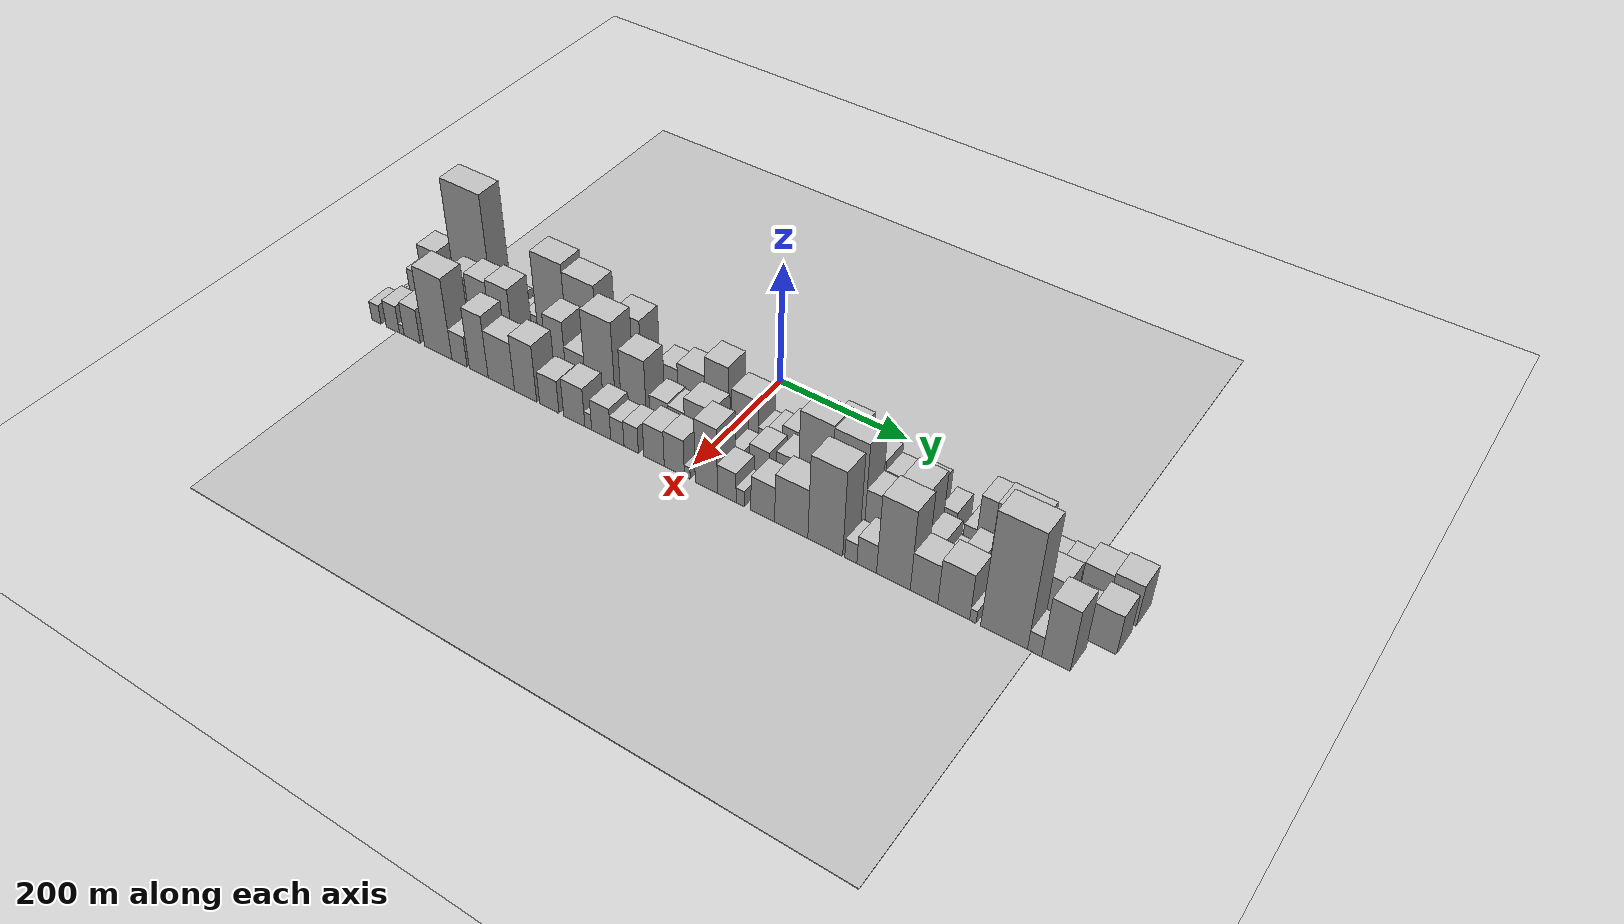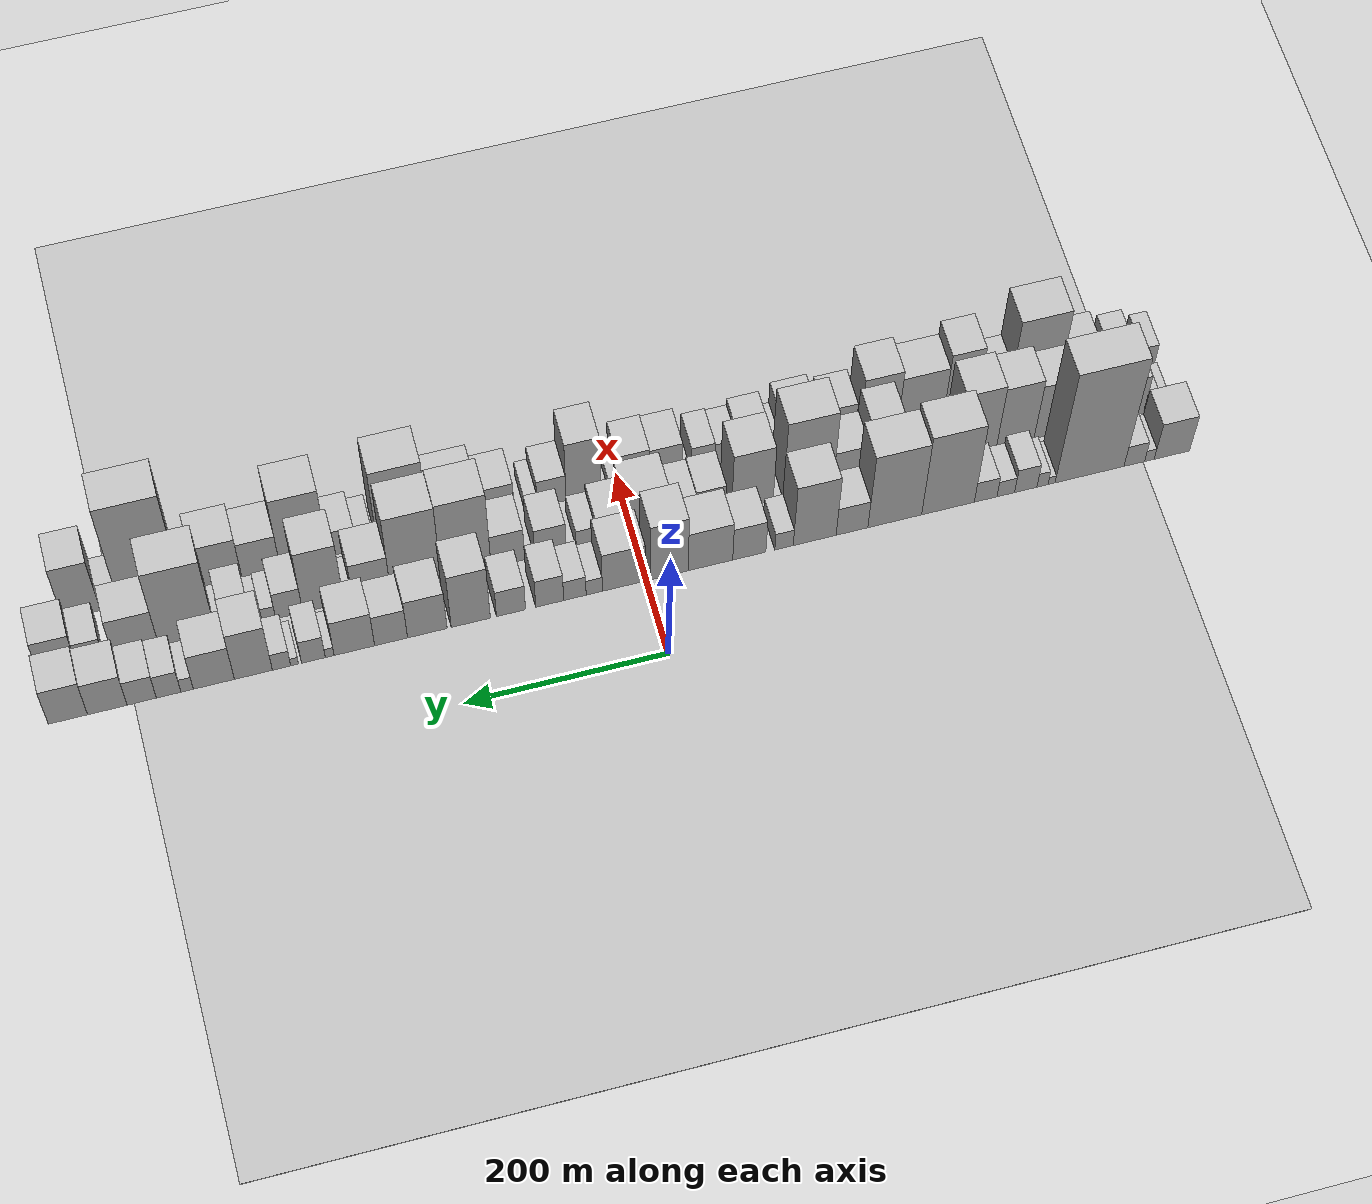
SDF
<?xml version="1.0" encoding="utf-8"?>

<sdf version="1.6">

   <world name="default">

      <gui fullscreen="0">

         <camera name="user_camera">

            <pose>-15 0 4.57585 0 0 0</pose>

            <view_controller>orbit</view_controller>

         </camera>

      </gui>

      <scene>

         <sky>

           <clouds>

             <speed>12</speed>

           </clouds>

         </sky>

         <ambient>0.4 0.4 0.4 1</ambient>

         <background>0.7 0.7 0.7 1</background>

         <shadows>1</shadows>

      </scene>

      <gravity>0 0 -9.8066</gravity>

      <magnetic_field>6e-06 2.3e-05 -4.2e-05</magnetic_field>

      <physics default="0" name="default_physics" type="ode">

         <ode>

            <solver>

               <type>quick</type>

               <iters>10</iters>

               <sor>1.0</sor>

               <use_dynamic_moi_rescaling>0</use_dynamic_moi_rescaling>

            </solver>

            <constraints>

               <cfm>0</cfm>

               <erp>0.2</erp>

               <contact_max_correcting_vel>100</contact_max_correcting_vel>

               <contact_surface_layer>0.001</contact_surface_layer>

            </constraints>

         </ode>

         <max_step_size>0.004</max_step_size>

         <real_time_factor>1</real_time_factor>

         <real_time_update_rate>250</real_time_update_rate>

      </physics>

      <light name="sun" type="directional">

         <cast_shadows>1</cast_shadows>

         <pose>0 0 10 0 0 0</pose>

         <diffuse>0.8 0.8 0.8 1</diffuse>

         <specular>0.2 0.2 0.2 1</specular>

         <attenuation>

            <range>1000</range>

            <constant>0.9</constant>

            <linear>0.01</linear>

            <quadratic>0.001</quadratic>

         </attenuation>

         <direction>-0.5 0.1 -0.9</direction>

      </light>

      <include>

         <name>ground_plane_1</name>

         <uri>model://HANNAS_ground_plane</uri>

         <pose>0 0 0  0 0 0</pose>

      </include>

      <include>

         <name>ground_plane_2</name>

         <uri>model://HANNAS_ground_plane</uri>

         <pose>100 0 0  0 0 0</pose>

      </include>

      <model name="building_1">

         <static>1</static>

         <pose frame="">100.0000 -529.7918 0 0.000000 0.000000 0.000000</pose>

         <link name="link">

            <pose frame="">0 0 34.50 0 0 0</pose>

            <collision name="collision">

               <geometry>

                  <box>

                     <size>40.0000 36.4164 69.0000</size>

                  </box>

               </geometry>

               <max_contacts>10</max_contacts>

               <surface>

                  <contact>

                     <ode/>

                  </contact>

                  <bounce/>

                  <friction>

                     <torsional>

                        <ode/>

                     </torsional>

                     <ode/>

                  </friction>

               </surface>

            </collision>

            <visual name="visual">

               <cast_shadows>0</cast_shadows>

               <geometry>

                  <box>

                     <size>40.0000 36.4164 69.0000</size>

                  </box>

               </geometry>

               <material>

                  <script>

                     <uri>model://HANNAS_wall/materials/scripts</uri>

                     <uri>model://HANNAS_wall/materials/textures</uri>

                     <name>vrc/HANNAS_wall</name>

                  </script>

               </material>

            </visual>

            <self_collide>0</self_collide>

            <enable_wind>0</enable_wind>

            <kinematic>0</kinematic>

         </link>

      </model>

      <model name="building_2">

         <static>1</static>

         <pose frame="">100.0000 -506.6692 0 0.000000 0.000000 0.000000</pose>

         <link name="link">

            <pose frame="">0 0 10.50 0 0 0</pose>

            <collision name="collision">

               <geometry>

                  <box>

                     <size>40.0000 9.8289 21.0000</size>

                  </box>

               </geometry>

               <max_contacts>10</max_contacts>

               <surface>

                  <contact>

                     <ode/>

                  </contact>

                  <bounce/>

                  <friction>

                     <torsional>

                        <ode/>

                     </torsional>

                     <ode/>

                  </friction>

               </surface>

            </collision>

            <visual name="visual">

               <cast_shadows>0</cast_shadows>

               <geometry>

                  <box>

                     <size>40.0000 9.8289 21.0000</size>

                  </box>

               </geometry>

               <material>

                  <script>

                     <uri>model://HANNAS_wall/materials/scripts</uri>

                     <uri>model://HANNAS_wall/materials/textures</uri>

                     <name>vrc/HANNAS_wall</name>

                  </script>

               </material>

            </visual>

            <self_collide>0</self_collide>

            <enable_wind>0</enable_wind>

            <kinematic>0</kinematic>

         </link>

      </model>

      <model name="building_3">

         <static>1</static>

         <pose frame="">100.0000 -491.1735 0 0.000000 0.000000 0.000000</pose>

         <link name="link">

            <pose frame="">0 0 19.50 0 0 0</pose>

            <collision name="collision">

               <geometry>

                  <box>

                     <size>40.0000 21.1624 39.0000</size>

                  </box>

               </geometry>

               <max_contacts>10</max_contacts>

               <surface>

                  <contact>

                     <ode/>

                  </contact>

                  <bounce/>

                  <friction>

                     <torsional>

                        <ode/>

                     </torsional>

                     <ode/>

                  </friction>

               </surface>

            </collision>

            <visual name="visual">

               <cast_shadows>0</cast_shadows>

               <geometry>

                  <box>

                     <size>40.0000 21.1624 39.0000</size>

                  </box>

               </geometry>

               <material>

                  <script>

                     <uri>model://HANNAS_wall/materials/scripts</uri>

                     <uri>model://HANNAS_wall/materials/textures</uri>

                     <name>vrc/HANNAS_wall</name>

                  </script>

               </material>

            </visual>

            <self_collide>0</self_collide>

            <enable_wind>0</enable_wind>

            <kinematic>0</kinematic>

         </link>

      </model>

      <model name="building_4">

         <static>1</static>

         <pose frame="">100.0000 -445.2849 0 0.000000 0.000000 0.000000</pose>

         <link name="link">

            <pose frame="">0 0 105.00 0 0 0</pose>

            <collision name="collision">

               <geometry>

                  <box>

                     <size>40.0000 70.6147 210.0000</size>

                  </box>

               </geometry>

               <max_contacts>10</max_contacts>

               <surface>

                  <contact>

                     <ode/>

                  </contact>

                  <bounce/>

                  <friction>

                     <torsional>

                        <ode/>

                     </torsional>

                     <ode/>

                  </friction>

               </surface>

            </collision>

            <visual name="visual">

               <cast_shadows>0</cast_shadows>

               <geometry>

                  <box>

                     <size>40.0000 70.6147 210.0000</size>

                  </box>

               </geometry>

               <material>

                  <script>

                     <uri>model://HANNAS_wall/materials/scripts</uri>

                     <uri>model://HANNAS_wall/materials/textures</uri>

                     <name>vrc/HANNAS_wall</name>

                  </script>

               </material>

            </visual>

            <self_collide>0</self_collide>

            <enable_wind>0</enable_wind>

            <kinematic>0</kinematic>

         </link>

      </model>

      <model name="building_5">

         <static>1</static>

         <pose frame="">100.0000 -406.3742 0 0.000000 0.000000 0.000000</pose>

         <link name="link">

            <pose frame="">0 0 7.50 0 0 0</pose>

            <collision name="collision">

               <geometry>

                  <box>

                     <size>40.0000 7.2066 15.0000</size>

                  </box>

               </geometry>

               <max_contacts>10</max_contacts>

               <surface>

                  <contact>

                     <ode/>

                  </contact>

                  <bounce/>

                  <friction>

                     <torsional>

                        <ode/>

                     </torsional>

                     <ode/>

                  </friction>

               </surface>

            </collision>

            <visual name="visual">

               <cast_shadows>0</cast_shadows>

               <geometry>

                  <box>

                     <size>40.0000 7.2066 15.0000</size>

                  </box>

               </geometry>

               <material>

                  <script>

                     <uri>model://HANNAS_wall/materials/scripts</uri>

                     <uri>model://HANNAS_wall/materials/textures</uri>

                     <name>vrc/HANNAS_wall</name>

                  </script>

               </material>

            </visual>

            <self_collide>0</self_collide>

            <enable_wind>0</enable_wind>

            <kinematic>0</kinematic>

         </link>

      </model>

      <model name="building_6">

         <static>1</static>

         <pose frame="">100.0000 -397.1257 0 0.000000 0.000000 0.000000</pose>

         <link name="link">

            <pose frame="">0 0 13.50 0 0 0</pose>

            <collision name="collision">

               <geometry>

                  <box>

                     <size>40.0000 11.2906 27.0000</size>

                  </box>

               </geometry>

               <max_contacts>10</max_contacts>

               <surface>

                  <contact>

                     <ode/>

                  </contact>

                  <bounce/>

                  <friction>

                     <torsional>

                        <ode/>

                     </torsional>

                     <ode/>

                  </friction>

               </surface>

            </collision>

            <visual name="visual">

               <cast_shadows>0</cast_shadows>

               <geometry>

                  <box>

                     <size>40.0000 11.2906 27.0000</size>

                  </box>

               </geometry>

               <material>

                  <script>

                     <uri>model://HANNAS_wall/materials/scripts</uri>

                     <uri>model://HANNAS_wall/materials/textures</uri>

                     <name>vrc/HANNAS_wall</name>

                  </script>

               </material>

            </visual>

            <self_collide>0</self_collide>

            <enable_wind>0</enable_wind>

            <kinematic>0</kinematic>

         </link>

      </model>

      <model name="building_7">

         <static>1</static>

         <pose frame="">100.0000 -380.0836 0 0.000000 0.000000 0.000000</pose>

         <link name="link">

            <pose frame="">0 0 22.50 0 0 0</pose>

            <collision name="collision">

               <geometry>

                  <box>

                     <size>40.0000 22.7934 45.0000</size>

                  </box>

               </geometry>

               <max_contacts>10</max_contacts>

               <surface>

                  <contact>

                     <ode/>

                  </contact>

                  <bounce/>

                  <friction>

                     <torsional>

                        <ode/>

                     </torsional>

                     <ode/>

                  </friction>

               </surface>

            </collision>

            <visual name="visual">

               <cast_shadows>0</cast_shadows>

               <geometry>

                  <box>

                     <size>40.0000 22.7934 45.0000</size>

                  </box>

               </geometry>

               <material>

                  <script>

                     <uri>model://HANNAS_wall/materials/scripts</uri>

                     <uri>model://HANNAS_wall/materials/textures</uri>

                     <name>vrc/HANNAS_wall</name>

                  </script>

               </material>

            </visual>

            <self_collide>0</self_collide>

            <enable_wind>0</enable_wind>

            <kinematic>0</kinematic>

         </link>

      </model>

      <model name="building_8">

         <static>1</static>

         <pose frame="">100.0000 -359.7217 0 0.000000 0.000000 0.000000</pose>

         <link name="link">

            <pose frame="">0 0 15.00 0 0 0</pose>

            <collision name="collision">

               <geometry>

                  <box>

                     <size>40.0000 17.9304 30.0000</size>

                  </box>

               </geometry>

               <max_contacts>10</max_contacts>

               <surface>

                  <contact>

                     <ode/>

                  </contact>

                  <bounce/>

                  <friction>

                     <torsional>

                        <ode/>

                     </torsional>

                     <ode/>

                  </friction>

               </surface>

            </collision>

            <visual name="visual">

               <cast_shadows>0</cast_shadows>

               <geometry>

                  <box>

                     <size>40.0000 17.9304 30.0000</size>

                  </box>

               </geometry>

               <material>

                  <script>

                     <uri>model://HANNAS_wall/materials/scripts</uri>

                     <uri>model://HANNAS_wall/materials/textures</uri>

                     <name>vrc/HANNAS_wall</name>

                  </script>

               </material>

            </visual>

            <self_collide>0</self_collide>

            <enable_wind>0</enable_wind>

            <kinematic>0</kinematic>

         </link>

      </model>

      <model name="building_9">

         <static>1</static>

         <pose frame="">100.0000 -339.2862 0 0.000000 0.000000 0.000000</pose>

         <link name="link">

            <pose frame="">0 0 19.50 0 0 0</pose>

            <collision name="collision">

               <geometry>

                  <box>

                     <size>40.0000 22.9406 39.0000</size>

                  </box>

               </geometry>

               <max_contacts>10</max_contacts>

               <surface>

                  <contact>

                     <ode/>

                  </contact>

                  <bounce/>

                  <friction>

                     <torsional>

                        <ode/>

                     </torsional>

                     <ode/>

                  </friction>

               </surface>

            </collision>

            <visual name="visual">

               <cast_shadows>0</cast_shadows>

               <geometry>

                  <box>

                     <size>40.0000 22.9406 39.0000</size>

                  </box>

               </geometry>

               <material>

                  <script>

                     <uri>model://HANNAS_wall/materials/scripts</uri>

                     <uri>model://HANNAS_wall/materials/textures</uri>

                     <name>vrc/HANNAS_wall</name>

                  </script>

               </material>

            </visual>

            <self_collide>0</self_collide>

            <enable_wind>0</enable_wind>

            <kinematic>0</kinematic>

         </link>

      </model>

      <model name="building_10">

         <static>1</static>

         <pose frame="">100.0000 -301.1103 0 0.000000 0.000000 0.000000</pose>

         <link name="link">

            <pose frame="">0 0 76.50 0 0 0</pose>

            <collision name="collision">

               <geometry>

                  <box>

                     <size>40.0000 53.4113 153.0000</size>

                  </box>

               </geometry>

               <max_contacts>10</max_contacts>

               <surface>

                  <contact>

                     <ode/>

                  </contact>

                  <bounce/>

                  <friction>

                     <torsional>

                        <ode/>

                     </torsional>

                     <ode/>

                  </friction>

               </surface>

            </collision>

            <visual name="visual">

               <cast_shadows>0</cast_shadows>

               <geometry>

                  <box>

                     <size>40.0000 53.4113 153.0000</size>

                  </box>

               </geometry>

               <material>

                  <script>

                     <uri>model://HANNAS_wall/materials/scripts</uri>

                     <uri>model://HANNAS_wall/materials/textures</uri>

                     <name>vrc/HANNAS_wall</name>

                  </script>

               </material>

            </visual>

            <self_collide>0</self_collide>

            <enable_wind>0</enable_wind>

            <kinematic>0</kinematic>

         </link>

      </model>

      <model name="building_11">

         <static>1</static>

         <pose frame="">100.0000 -247.2647 0 0.000000 0.000000 0.000000</pose>

         <link name="link">

            <pose frame="">0 0 70.50 0 0 0</pose>

            <collision name="collision">

               <geometry>

                  <box>

                     <size>40.0000 54.2798 141.0000</size>

                  </box>

               </geometry>

               <max_contacts>10</max_contacts>

               <surface>

                  <contact>

                     <ode/>

                  </contact>

                  <bounce/>

                  <friction>

                     <torsional>

                        <ode/>

                     </torsional>

                     <ode/>

                  </friction>

               </surface>

            </collision>

            <visual name="visual">

               <cast_shadows>0</cast_shadows>

               <geometry>

                  <box>

                     <size>40.0000 54.2798 141.0000</size>

                  </box>

               </geometry>

               <material>

                  <script>

                     <uri>model://HANNAS_wall/materials/scripts</uri>

                     <uri>model://HANNAS_wall/materials/textures</uri>

                     <name>vrc/HANNAS_wall</name>

                  </script>

               </material>

            </visual>

            <self_collide>0</self_collide>

            <enable_wind>0</enable_wind>

            <kinematic>0</kinematic>

         </link>

      </model>

      <model name="building_12">

         <static>1</static>

         <pose frame="">100.0000 -204.1808 0 0.000000 0.000000 0.000000</pose>

         <link name="link">

            <pose frame="">0 0 27.00 0 0 0</pose>

            <collision name="collision">

               <geometry>

                  <box>

                     <size>40.0000 31.8879 54.0000</size>

                  </box>

               </geometry>

               <max_contacts>10</max_contacts>

               <surface>

                  <contact>

                     <ode/>

                  </contact>

                  <bounce/>

                  <friction>

                     <torsional>

                        <ode/>

                     </torsional>

                     <ode/>

                  </friction>

               </surface>

            </collision>

            <visual name="visual">

               <cast_shadows>0</cast_shadows>

               <geometry>

                  <box>

                     <size>40.0000 31.8879 54.0000</size>

                  </box>

               </geometry>

               <material>

                  <script>

                     <uri>model://HANNAS_wall/materials/scripts</uri>

                     <uri>model://HANNAS_wall/materials/textures</uri>

                     <name>vrc/HANNAS_wall</name>

                  </script>

               </material>

            </visual>

            <self_collide>0</self_collide>

            <enable_wind>0</enable_wind>

            <kinematic>0</kinematic>

         </link>

      </model>

      <model name="building_13">

         <static>1</static>

         <pose frame="">100.0000 -166.6848 0 0.000000 0.000000 0.000000</pose>

         <link name="link">

            <pose frame="">0 0 58.50 0 0 0</pose>

            <collision name="collision">

               <geometry>

                  <box>

                     <size>40.0000 43.1041 117.0000</size>

                  </box>

               </geometry>

               <max_contacts>10</max_contacts>

               <surface>

                  <contact>

                     <ode/>

                  </contact>

                  <bounce/>

                  <friction>

                     <torsional>

                        <ode/>

                     </torsional>

                     <ode/>

                  </friction>

               </surface>

            </collision>

            <visual name="visual">

               <cast_shadows>0</cast_shadows>

               <geometry>

                  <box>

                     <size>40.0000 43.1041 117.0000</size>

                  </box>

               </geometry>

               <material>

                  <script>

                     <uri>model://HANNAS_wall/materials/scripts</uri>

                     <uri>model://HANNAS_wall/materials/textures</uri>

                     <name>vrc/HANNAS_wall</name>

                  </script>

               </material>

            </visual>

            <self_collide>0</self_collide>

            <enable_wind>0</enable_wind>

            <kinematic>0</kinematic>

         </link>

      </model>

      <model name="building_14">

         <static>1</static>

         <pose frame="">100.0000 -135.9264 0 0.000000 0.000000 0.000000</pose>

         <link name="link">

            <pose frame="">0 0 16.50 0 0 0</pose>

            <collision name="collision">

               <geometry>

                  <box>

                     <size>40.0000 18.4126 33.0000</size>

                  </box>

               </geometry>

               <max_contacts>10</max_contacts>

               <surface>

                  <contact>

                     <ode/>

                  </contact>

                  <bounce/>

                  <friction>

                     <torsional>

                        <ode/>

                     </torsional>

                     <ode/>

                  </friction>

               </surface>

            </collision>

            <visual name="visual">

               <cast_shadows>0</cast_shadows>

               <geometry>

                  <box>

                     <size>40.0000 18.4126 33.0000</size>

                  </box>

               </geometry>

               <material>

                  <script>

                     <uri>model://HANNAS_wall/materials/scripts</uri>

                     <uri>model://HANNAS_wall/materials/textures</uri>

                     <name>vrc/HANNAS_wall</name>

                  </script>

               </material>

            </visual>

            <self_collide>0</self_collide>

            <enable_wind>0</enable_wind>

            <kinematic>0</kinematic>

         </link>

      </model>

      <model name="building_15">

         <static>1</static>

         <pose frame="">100.0000 -101.1869 0 0.000000 0.000000 0.000000</pose>

         <link name="link">

            <pose frame="">0 0 31.50 0 0 0</pose>

            <collision name="collision">

               <geometry>

                  <box>

                     <size>40.0000 33.0664 63.0000</size>

                  </box>

               </geometry>

               <max_contacts>10</max_contacts>

               <surface>

                  <contact>

                     <ode/>

                  </contact>

                  <bounce/>

                  <friction>

                     <torsional>

                        <ode/>

                     </torsional>

                     <ode/>

                  </friction>

               </surface>

            </collision>

            <visual name="visual">

               <cast_shadows>0</cast_shadows>

               <geometry>

                  <box>

                     <size>40.0000 33.0664 63.0000</size>

                  </box>

               </geometry>

               <material>

                  <script>

                     <uri>model://HANNAS_wall/materials/scripts</uri>

                     <uri>model://HANNAS_wall/materials/textures</uri>

                     <name>vrc/HANNAS_wall</name>

                  </script>

               </material>

            </visual>

            <self_collide>0</self_collide>

            <enable_wind>0</enable_wind>

            <kinematic>0</kinematic>

         </link>

      </model>

      <model name="building_16">

         <static>1</static>

         <pose frame="">100.0000 -62.4404 0 0.000000 0.000000 0.000000</pose>

         <link name="link">

            <pose frame="">0 0 37.50 0 0 0</pose>

            <collision name="collision">

               <geometry>

                  <box>

                     <size>40.0000 44.4265 75.0000</size>

                  </box>

               </geometry>

               <max_contacts>10</max_contacts>

               <surface>

                  <contact>

                     <ode/>

                  </contact>

                  <bounce/>

                  <friction>

                     <torsional>

                        <ode/>

                     </torsional>

                     <ode/>

                  </friction>

               </surface>

            </collision>

            <visual name="visual">

               <cast_shadows>0</cast_shadows>

               <geometry>

                  <box>

                     <size>40.0000 44.4265 75.0000</size>

                  </box>

               </geometry>

               <material>

                  <script>

                     <uri>model://HANNAS_wall/materials/scripts</uri>

                     <uri>model://HANNAS_wall/materials/textures</uri>

                     <name>vrc/HANNAS_wall</name>

                  </script>

               </material>

            </visual>

            <self_collide>0</self_collide>

            <enable_wind>0</enable_wind>

            <kinematic>0</kinematic>

         </link>

      </model>

      <model name="building_17">

         <static>1</static>

         <pose frame="">100.0000 -21.3865 0 0.000000 0.000000 0.000000</pose>

         <link name="link">

            <pose frame="">0 0 54.00 0 0 0</pose>

            <collision name="collision">

               <geometry>

                  <box>

                     <size>40.0000 37.6813 108.0000</size>

                  </box>

               </geometry>

               <max_contacts>10</max_contacts>

               <surface>

                  <contact>

                     <ode/>

                  </contact>

                  <bounce/>

                  <friction>

                     <torsional>

                        <ode/>

                     </torsional>

                     <ode/>

                  </friction>

               </surface>

            </collision>

            <visual name="visual">

               <cast_shadows>0</cast_shadows>

               <geometry>

                  <box>

                     <size>40.0000 37.6813 108.0000</size>

                  </box>

               </geometry>

               <material>

                  <script>

                     <uri>model://HANNAS_wall/materials/scripts</uri>

                     <uri>model://HANNAS_wall/materials/textures</uri>

                     <name>vrc/HANNAS_wall</name>

                  </script>

               </material>

            </visual>

            <self_collide>0</self_collide>

            <enable_wind>0</enable_wind>

            <kinematic>0</kinematic>

         </link>

      </model>

      <model name="building_18">

         <static>1</static>

         <pose frame="">100.0000 23.6500 0 0.000000 0.000000 0.000000</pose>

         <link name="link">

            <pose frame="">0 0 37.50 0 0 0</pose>

            <collision name="collision">

               <geometry>

                  <box>

                     <size>40.0000 42.3919 75.0000</size>

                  </box>

               </geometry>

               <max_contacts>10</max_contacts>

               <surface>

                  <contact>

                     <ode/>

                  </contact>

                  <bounce/>

                  <friction>

                     <torsional>

                        <ode/>

                     </torsional>

                     <ode/>

                  </friction>

               </surface>

            </collision>

            <visual name="visual">

               <cast_shadows>0</cast_shadows>

               <geometry>

                  <box>

                     <size>40.0000 42.3919 75.0000</size>

                  </box>

               </geometry>

               <material>

                  <script>

                     <uri>model://HANNAS_wall/materials/scripts</uri>

                     <uri>model://HANNAS_wall/materials/textures</uri>

                     <name>vrc/HANNAS_wall</name>

                  </script>

               </material>

            </visual>

            <self_collide>0</self_collide>

            <enable_wind>0</enable_wind>

            <kinematic>0</kinematic>

         </link>

      </model>

      <model name="building_19">

         <static>1</static>

         <pose frame="">100.0000 52.8232 0 0.000000 0.000000 0.000000</pose>

         <link name="link">

            <pose frame="">0 0 15.00 0 0 0</pose>

            <collision name="collision">

               <geometry>

                  <box>

                     <size>40.0000 15.9544 30.0000</size>

                  </box>

               </geometry>

               <max_contacts>10</max_contacts>

               <surface>

                  <contact>

                     <ode/>

                  </contact>

                  <bounce/>

                  <friction>

                     <torsional>

                        <ode/>

                     </torsional>

                     <ode/>

                  </friction>

               </surface>

            </collision>

            <visual name="visual">

               <cast_shadows>0</cast_shadows>

               <geometry>

                  <box>

                     <size>40.0000 15.9544 30.0000</size>

                  </box>

               </geometry>

               <material>

                  <script>

                     <uri>model://HANNAS_wall/materials/scripts</uri>

                     <uri>model://HANNAS_wall/materials/textures</uri>

                     <name>vrc/HANNAS_wall</name>

                  </script>

               </material>

            </visual>

            <self_collide>0</self_collide>

            <enable_wind>0</enable_wind>

            <kinematic>0</kinematic>

         </link>

      </model>

      <model name="building_20">

         <static>1</static>

         <pose frame="">100.0000 71.8989 0 0.000000 0.000000 0.000000</pose>

         <link name="link">

            <pose frame="">0 0 19.50 0 0 0</pose>

            <collision name="collision">

               <geometry>

                  <box>

                     <size>40.0000 22.1970 39.0000</size>

                  </box>

               </geometry>

               <max_contacts>10</max_contacts>

               <surface>

                  <contact>

                     <ode/>

                  </contact>

                  <bounce/>

                  <friction>

                     <torsional>

                        <ode/>

                     </torsional>

                     <ode/>

                  </friction>

               </surface>

            </collision>

            <visual name="visual">

               <cast_shadows>0</cast_shadows>

               <geometry>

                  <box>

                     <size>40.0000 22.1970 39.0000</size>

                  </box>

               </geometry>

               <material>

                  <script>

                     <uri>model://HANNAS_wall/materials/scripts</uri>

                     <uri>model://HANNAS_wall/materials/textures</uri>

                     <name>vrc/HANNAS_wall</name>

                  </script>

               </material>

            </visual>

            <self_collide>0</self_collide>

            <enable_wind>0</enable_wind>

            <kinematic>0</kinematic>

         </link>

      </model>

      <model name="building_21">

         <static>1</static>

         <pose frame="">100.0000 96.7410 0 0.000000 0.000000 0.000000</pose>

         <link name="link">

            <pose frame="">0 0 27.00 0 0 0</pose>

            <collision name="collision">

               <geometry>

                  <box>

                     <size>40.0000 27.4872 54.0000</size>

                  </box>

               </geometry>

               <max_contacts>10</max_contacts>

               <surface>

                  <contact>

                     <ode/>

                  </contact>

                  <bounce/>

                  <friction>

                     <torsional>

                        <ode/>

                     </torsional>

                     <ode/>

                  </friction>

               </surface>

            </collision>

            <visual name="visual">

               <cast_shadows>0</cast_shadows>

               <geometry>

                  <box>

                     <size>40.0000 27.4872 54.0000</size>

                  </box>

               </geometry>

               <material>

                  <script>

                     <uri>model://HANNAS_wall/materials/scripts</uri>

                     <uri>model://HANNAS_wall/materials/textures</uri>

                     <name>vrc/HANNAS_wall</name>

                  </script>

               </material>

            </visual>

            <self_collide>0</self_collide>

            <enable_wind>0</enable_wind>

            <kinematic>0</kinematic>

         </link>

      </model>

      <model name="building_22">

         <static>1</static>

         <pose frame="">100.0000 134.7807 0 0.000000 0.000000 0.000000</pose>

         <link name="link">

            <pose frame="">0 0 25.50 0 0 0</pose>

            <collision name="collision">

               <geometry>

                  <box>

                     <size>40.0000 28.5921 51.0000</size>

                  </box>

               </geometry>

               <max_contacts>10</max_contacts>

               <surface>

                  <contact>

                     <ode/>

                  </contact>

                  <bounce/>

                  <friction>

                     <torsional>

                        <ode/>

                     </torsional>

                     <ode/>

                  </friction>

               </surface>

            </collision>

            <visual name="visual">

               <cast_shadows>0</cast_shadows>

               <geometry>

                  <box>

                     <size>40.0000 28.5921 51.0000</size>

                  </box>

               </geometry>

               <material>

                  <script>

                     <uri>model://HANNAS_wall/materials/scripts</uri>

                     <uri>model://HANNAS_wall/materials/textures</uri>

                     <name>vrc/HANNAS_wall</name>

                  </script>

               </material>

            </visual>

            <self_collide>0</self_collide>

            <enable_wind>0</enable_wind>

            <kinematic>0</kinematic>

         </link>

      </model>

      <model name="building_23">

         <static>1</static>

         <pose frame="">100.0000 174.2291 0 0.000000 0.000000 0.000000</pose>

         <link name="link">

            <pose frame="">0 0 52.50 0 0 0</pose>

            <collision name="collision">

               <geometry>

                  <box>

                     <size>40.0000 38.3047 105.0000</size>

                  </box>

               </geometry>

               <max_contacts>10</max_contacts>

               <surface>

                  <contact>

                     <ode/>

                  </contact>

                  <bounce/>

                  <friction>

                     <torsional>

                        <ode/>

                     </torsional>

                     <ode/>

                  </friction>

               </surface>

            </collision>

            <visual name="visual">

               <cast_shadows>0</cast_shadows>

               <geometry>

                  <box>

                     <size>40.0000 38.3047 105.0000</size>

                  </box>

               </geometry>

               <material>

                  <script>

                     <uri>model://HANNAS_wall/materials/scripts</uri>

                     <uri>model://HANNAS_wall/materials/textures</uri>

                     <name>vrc/HANNAS_wall</name>

                  </script>

               </material>

            </visual>

            <self_collide>0</self_collide>

            <enable_wind>0</enable_wind>

            <kinematic>0</kinematic>

         </link>

      </model>

      <model name="building_24">

         <static>1</static>

         <pose frame="">100.0000 216.7153 0 0.000000 0.000000 0.000000</pose>

         <link name="link">

            <pose frame="">0 0 37.50 0 0 0</pose>

            <collision name="collision">

               <geometry>

                  <box>

                     <size>40.0000 38.6677 75.0000</size>

                  </box>

               </geometry>

               <max_contacts>10</max_contacts>

               <surface>

                  <contact>

                     <ode/>

                  </contact>

                  <bounce/>

                  <friction>

                     <torsional>

                        <ode/>

                     </torsional>

                     <ode/>

                  </friction>

               </surface>

            </collision>

            <visual name="visual">

               <cast_shadows>0</cast_shadows>

               <geometry>

                  <box>

                     <size>40.0000 38.6677 75.0000</size>

                  </box>

               </geometry>

               <material>

                  <script>

                     <uri>model://HANNAS_wall/materials/scripts</uri>

                     <uri>model://HANNAS_wall/materials/textures</uri>

                     <name>vrc/HANNAS_wall</name>

                  </script>

               </material>

            </visual>

            <self_collide>0</self_collide>

            <enable_wind>0</enable_wind>

            <kinematic>0</kinematic>

         </link>

      </model>

      <model name="building_25">

         <static>1</static>

         <pose frame="">100.0000 252.0705 0 0.000000 0.000000 0.000000</pose>

         <link name="link">

            <pose frame="">0 0 30.00 0 0 0</pose>

            <collision name="collision">

               <geometry>

                  <box>

                     <size>40.0000 32.0428 60.0000</size>

                  </box>

               </geometry>

               <max_contacts>10</max_contacts>

               <surface>

                  <contact>

                     <ode/>

                  </contact>

                  <bounce/>

                  <friction>

                     <torsional>

                        <ode/>

                     </torsional>

                     <ode/>

                  </friction>

               </surface>

            </collision>

            <visual name="visual">

               <cast_shadows>0</cast_shadows>

               <geometry>

                  <box>

                     <size>40.0000 32.0428 60.0000</size>

                  </box>

               </geometry>

               <material>

                  <script>

                     <uri>model://HANNAS_wall/materials/scripts</uri>

                     <uri>model://HANNAS_wall/materials/textures</uri>

                     <name>vrc/HANNAS_wall</name>

                  </script>

               </material>

            </visual>

            <self_collide>0</self_collide>

            <enable_wind>0</enable_wind>

            <kinematic>0</kinematic>

         </link>

      </model>

      <model name="building_26">

         <static>1</static>

         <pose frame="">100.0000 287.7760 0 0.000000 0.000000 0.000000</pose>

         <link name="link">

            <pose frame="">0 0 34.50 0 0 0</pose>

            <collision name="collision">

               <geometry>

                  <box>

                     <size>40.0000 39.3682 69.0000</size>

                  </box>

               </geometry>

               <max_contacts>10</max_contacts>

               <surface>

                  <contact>

                     <ode/>

                  </contact>

                  <bounce/>

                  <friction>

                     <torsional>

                        <ode/>

                     </torsional>

                     <ode/>

                  </friction>

               </surface>

            </collision>

            <visual name="visual">

               <cast_shadows>0</cast_shadows>

               <geometry>

                  <box>

                     <size>40.0000 39.3682 69.0000</size>

                  </box>

               </geometry>

               <material>

                  <script>

                     <uri>model://HANNAS_wall/materials/scripts</uri>

                     <uri>model://HANNAS_wall/materials/textures</uri>

                     <name>vrc/HANNAS_wall</name>

                  </script>

               </material>

            </visual>

            <self_collide>0</self_collide>

            <enable_wind>0</enable_wind>

            <kinematic>0</kinematic>

         </link>

      </model>

      <model name="building_27">

         <static>1</static>

         <pose frame="">100.0000 311.7045 0 0.000000 0.000000 0.000000</pose>

         <link name="link">

            <pose frame="">0 0 9.00 0 0 0</pose>

            <collision name="collision">

               <geometry>

                  <box>

                     <size>40.0000 8.4889 18.0000</size>

                  </box>

               </geometry>

               <max_contacts>10</max_contacts>

               <surface>

                  <contact>

                     <ode/>

                  </contact>

                  <bounce/>

                  <friction>

                     <torsional>

                        <ode/>

                     </torsional>

                     <ode/>

                  </friction>

               </surface>

            </collision>

            <visual name="visual">

               <cast_shadows>0</cast_shadows>

               <geometry>

                  <box>

                     <size>40.0000 8.4889 18.0000</size>

                  </box>

               </geometry>

               <material>

                  <script>

                     <uri>model://HANNAS_wall/materials/scripts</uri>

                     <uri>model://HANNAS_wall/materials/textures</uri>

                     <name>vrc/HANNAS_wall</name>

                  </script>

               </material>

            </visual>

            <self_collide>0</self_collide>

            <enable_wind>0</enable_wind>

            <kinematic>0</kinematic>

         </link>

      </model>

      <model name="building_28">

         <static>1</static>

         <pose frame="">100.0000 327.4721 0 0.000000 0.000000 0.000000</pose>

         <link name="link">

            <pose frame="">0 0 22.50 0 0 0</pose>

            <collision name="collision">

               <geometry>

                  <box>

                     <size>40.0000 23.0463 45.0000</size>

                  </box>

               </geometry>

               <max_contacts>10</max_contacts>

               <surface>

                  <contact>

                     <ode/>

                  </contact>

                  <bounce/>

                  <friction>

                     <torsional>

                        <ode/>

                     </torsional>

                     <ode/>

                  </friction>

               </surface>

            </collision>

            <visual name="visual">

               <cast_shadows>0</cast_shadows>

               <geometry>

                  <box>

                     <size>40.0000 23.0463 45.0000</size>

                  </box>

               </geometry>

               <material>

                  <script>

                     <uri>model://HANNAS_wall/materials/scripts</uri>

                     <uri>model://HANNAS_wall/materials/textures</uri>

                     <name>vrc/HANNAS_wall</name>

                  </script>

               </material>

            </visual>

            <self_collide>0</self_collide>

            <enable_wind>0</enable_wind>

            <kinematic>0</kinematic>

         </link>

      </model>

      <model name="building_29">

         <static>1</static>

         <pose frame="">100.0000 345.7176 0 0.000000 0.000000 0.000000</pose>

         <link name="link">

            <pose frame="">0 0 7.50 0 0 0</pose>

            <collision name="collision">

               <geometry>

                  <box>

                     <size>40.0000 7.4447 15.0000</size>

                  </box>

               </geometry>

               <max_contacts>10</max_contacts>

               <surface>

                  <contact>

                     <ode/>

                  </contact>

                  <bounce/>

                  <friction>

                     <torsional>

                        <ode/>

                     </torsional>

                     <ode/>

                  </friction>

               </surface>

            </collision>

            <visual name="visual">

               <cast_shadows>0</cast_shadows>

               <geometry>

                  <box>

                     <size>40.0000 7.4447 15.0000</size>

                  </box>

               </geometry>

               <material>

                  <script>

                     <uri>model://HANNAS_wall/materials/scripts</uri>

                     <uri>model://HANNAS_wall/materials/textures</uri>

                     <name>vrc/HANNAS_wall</name>

                  </script>

               </material>

            </visual>

            <self_collide>0</self_collide>

            <enable_wind>0</enable_wind>

            <kinematic>0</kinematic>

         </link>

      </model>

      <model name="building_30">

         <static>1</static>

         <pose frame="">100.0000 358.3131 0 0.000000 0.000000 0.000000</pose>

         <link name="link">

            <pose frame="">0 0 16.50 0 0 0</pose>

            <collision name="collision">

               <geometry>

                  <box>

                     <size>40.0000 17.7463 33.0000</size>

                  </box>

               </geometry>

               <max_contacts>10</max_contacts>

               <surface>

                  <contact>

                     <ode/>

                  </contact>

                  <bounce/>

                  <friction>

                     <torsional>

                        <ode/>

                     </torsional>

                     <ode/>

                  </friction>

               </surface>

            </collision>

            <visual name="visual">

               <cast_shadows>0</cast_shadows>

               <geometry>

                  <box>

                     <size>40.0000 17.7463 33.0000</size>

                  </box>

               </geometry>

               <material>

                  <script>

                     <uri>model://HANNAS_wall/materials/scripts</uri>

                     <uri>model://HANNAS_wall/materials/textures</uri>

                     <name>vrc/HANNAS_wall</name>

                  </script>

               </material>

            </visual>

            <self_collide>0</self_collide>

            <enable_wind>0</enable_wind>

            <kinematic>0</kinematic>

         </link>

      </model>

      <model name="building_31">

         <static>1</static>

         <pose frame="">100.0000 385.5132 0 0.000000 0.000000 0.000000</pose>

         <link name="link">

            <pose frame="">0 0 46.50 0 0 0</pose>

            <collision name="collision">

               <geometry>

                  <box>

                     <size>40.0000 36.6539 93.0000</size>

                  </box>

               </geometry>

               <max_contacts>10</max_contacts>

               <surface>

                  <contact>

                     <ode/>

                  </contact>

                  <bounce/>

                  <friction>

                     <torsional>

                        <ode/>

                     </torsional>

                     <ode/>

                  </friction>

               </surface>

            </collision>

            <visual name="visual">

               <cast_shadows>0</cast_shadows>

               <geometry>

                  <box>

                     <size>40.0000 36.6539 93.0000</size>

                  </box>

               </geometry>

               <material>

                  <script>

                     <uri>model://HANNAS_wall/materials/scripts</uri>

                     <uri>model://HANNAS_wall/materials/textures</uri>

                     <name>vrc/HANNAS_wall</name>

                  </script>

               </material>

            </visual>

            <self_collide>0</self_collide>

            <enable_wind>0</enable_wind>

            <kinematic>0</kinematic>

         </link>

      </model>

      <model name="building_32">

         <static>1</static>

         <pose frame="">100.0000 423.6090 0 0.000000 0.000000 0.000000</pose>

         <link name="link">

            <pose frame="">0 0 34.50 0 0 0</pose>

            <collision name="collision">

               <geometry>

                  <box>

                     <size>40.0000 39.5377 69.0000</size>

                  </box>

               </geometry>

               <max_contacts>10</max_contacts>

               <surface>

                  <contact>

                     <ode/>

                  </contact>

                  <bounce/>

                  <friction>

                     <torsional>

                        <ode/>

                     </torsional>

                     <ode/>

                  </friction>

               </surface>

            </collision>

            <visual name="visual">

               <cast_shadows>0</cast_shadows>

               <geometry>

                  <box>

                     <size>40.0000 39.5377 69.0000</size>

                  </box>

               </geometry>

               <material>

                  <script>

                     <uri>model://HANNAS_wall/materials/scripts</uri>

                     <uri>model://HANNAS_wall/materials/textures</uri>

                     <name>vrc/HANNAS_wall</name>

                  </script>

               </material>

            </visual>

            <self_collide>0</self_collide>

            <enable_wind>0</enable_wind>

            <kinematic>0</kinematic>

         </link>

      </model>

      <model name="building_33">

         <static>1</static>

         <pose frame="">100.0000 449.3270 0 0.000000 0.000000 0.000000</pose>

         <link name="link">

            <pose frame="">0 0 13.50 0 0 0</pose>

            <collision name="collision">

               <geometry>

                  <box>

                     <size>40.0000 11.8984 27.0000</size>

                  </box>

               </geometry>

               <max_contacts>10</max_contacts>

               <surface>

                  <contact>

                     <ode/>

                  </contact>

                  <bounce/>

                  <friction>

                     <torsional>

                        <ode/>

                     </torsional>

                     <ode/>

                  </friction>

               </surface>

            </collision>

            <visual name="visual">

               <cast_shadows>0</cast_shadows>

               <geometry>

                  <box>

                     <size>40.0000 11.8984 27.0000</size>

                  </box>

               </geometry>

               <material>

                  <script>

                     <uri>model://HANNAS_wall/materials/scripts</uri>

                     <uri>model://HANNAS_wall/materials/textures</uri>

                     <name>vrc/HANNAS_wall</name>

                  </script>

               </material>

            </visual>

            <self_collide>0</self_collide>

            <enable_wind>0</enable_wind>

            <kinematic>0</kinematic>

         </link>

      </model>

      <model name="building_34">

         <static>1</static>

         <pose frame="">100.0000 467.0291 0 0.000000 0.000000 0.000000</pose>

         <link name="link">

            <pose frame="">0 0 22.50 0 0 0</pose>

            <collision name="collision">

               <geometry>

                  <box>

                     <size>40.0000 23.5057 45.0000</size>

                  </box>

               </geometry>

               <max_contacts>10</max_contacts>

               <surface>

                  <contact>

                     <ode/>

                  </contact>

                  <bounce/>

                  <friction>

                     <torsional>

                        <ode/>

                     </torsional>

                     <ode/>

                  </friction>

               </surface>

            </collision>

            <visual name="visual">

               <cast_shadows>0</cast_shadows>

               <geometry>

                  <box>

                     <size>40.0000 23.5057 45.0000</size>

                  </box>

               </geometry>

               <material>

                  <script>

                     <uri>model://HANNAS_wall/materials/scripts</uri>

                     <uri>model://HANNAS_wall/materials/textures</uri>

                     <name>vrc/HANNAS_wall</name>

                  </script>

               </material>

            </visual>

            <self_collide>0</self_collide>

            <enable_wind>0</enable_wind>

            <kinematic>0</kinematic>

         </link>

      </model>

      <model name="building_35">

         <static>1</static>

         <pose frame="">100.0000 492.8434 0 0.000000 0.000000 0.000000</pose>

         <link name="link">

            <pose frame="">0 0 24.00 0 0 0</pose>

            <collision name="collision">

               <geometry>

                  <box>

                     <size>40.0000 28.1228 48.0000</size>

                  </box>

               </geometry>

               <max_contacts>10</max_contacts>

               <surface>

                  <contact>

                     <ode/>

                  </contact>

                  <bounce/>

                  <friction>

                     <torsional>

                        <ode/>

                     </torsional>

                     <ode/>

                  </friction>

               </surface>

            </collision>

            <visual name="visual">

               <cast_shadows>0</cast_shadows>

               <geometry>

                  <box>

                     <size>40.0000 28.1228 48.0000</size>

                  </box>

               </geometry>

               <material>

                  <script>

                     <uri>model://HANNAS_wall/materials/scripts</uri>

                     <uri>model://HANNAS_wall/materials/textures</uri>

                     <name>vrc/HANNAS_wall</name>

                  </script>

               </material>

            </visual>

            <self_collide>0</self_collide>

            <enable_wind>0</enable_wind>

            <kinematic>0</kinematic>

         </link>

      </model>

      <model name="building_36">

         <static>1</static>

         <pose frame="">100.0000 525.7627 0 0.000000 0.000000 0.000000</pose>

         <link name="link">

            <pose frame="">0 0 31.50 0 0 0</pose>

            <collision name="collision">

               <geometry>

                  <box>

                     <size>40.0000 37.7156 63.0000</size>

                  </box>

               </geometry>

               <max_contacts>10</max_contacts>

               <surface>

                  <contact>

                     <ode/>

                  </contact>

                  <bounce/>

                  <friction>

                     <torsional>

                        <ode/>

                     </torsional>

                     <ode/>

                  </friction>

               </surface>

            </collision>

            <visual name="visual">

               <cast_shadows>0</cast_shadows>

               <geometry>

                  <box>

                     <size>40.0000 37.7156 63.0000</size>

                  </box>

               </geometry>

               <material>

                  <script>

                     <uri>model://HANNAS_wall/materials/scripts</uri>

                     <uri>model://HANNAS_wall/materials/textures</uri>

                     <name>vrc/HANNAS_wall</name>

                  </script>

               </material>

            </visual>

            <self_collide>0</self_collide>

            <enable_wind>0</enable_wind>

            <kinematic>0</kinematic>

         </link>

      </model>

      <model name="building_37">

         <static>1</static>

         <pose frame="">100.0000 563.3392 0 0.000000 0.000000 0.000000</pose>

         <link name="link">

            <pose frame="">0 0 34.50 0 0 0</pose>

            <collision name="collision">

               <geometry>

                  <box>

                     <size>40.0000 37.4375 69.0000</size>

                  </box>

               </geometry>

               <max_contacts>10</max_contacts>

               <surface>

                  <contact>

                     <ode/>

                  </contact>

                  <bounce/>

                  <friction>

                     <torsional>

                        <ode/>

                     </torsional>

                     <ode/>

                  </friction>

               </surface>

            </collision>

            <visual name="visual">

               <cast_shadows>0</cast_shadows>

               <geometry>

                  <box>

                     <size>40.0000 37.4375 69.0000</size>

                  </box>

               </geometry>

               <material>

                  <script>

                     <uri>model://HANNAS_wall/materials/scripts</uri>

                     <uri>model://HANNAS_wall/materials/textures</uri>

                     <name>vrc/HANNAS_wall</name>

                  </script>

               </material>

            </visual>

            <self_collide>0</self_collide>

            <enable_wind>0</enable_wind>

            <kinematic>0</kinematic>

         </link>

      </model>

      <model name="building_38">

         <static>1</static>

         <pose frame="">152.0000 -537.8394 0 0.000000 0.000000 0.000000</pose>

         <link name="link">

            <pose frame="">0 0 10.50 0 0 0</pose>

            <collision name="collision">

               <geometry>

                  <box>

                     <size>40.0000 10.3213 21.0000</size>

                  </box>

               </geometry>

               <max_contacts>10</max_contacts>

               <surface>

                  <contact>

                     <ode/>

                  </contact>

                  <bounce/>

                  <friction>

                     <torsional>

                        <ode/>

                     </torsional>

                     <ode/>

                  </friction>

               </surface>

            </collision>

            <visual name="visual">

               <cast_shadows>0</cast_shadows>

               <geometry>

                  <box>

                     <size>40.0000 10.3213 21.0000</size>

                  </box>

               </geometry>

               <material>

                  <script>

                     <uri>model://HANNAS_wall/materials/scripts</uri>

                     <uri>model://HANNAS_wall/materials/textures</uri>

                     <name>vrc/HANNAS_wall</name>

                  </script>

               </material>

            </visual>

            <self_collide>0</self_collide>

            <enable_wind>0</enable_wind>

            <kinematic>0</kinematic>

         </link>

      </model>

      <model name="building_39">

         <static>1</static>

         <pose frame="">152.0000 -526.9172 0 0.000000 0.000000 0.000000</pose>

         <link name="link">

            <pose frame="">0 0 13.50 0 0 0</pose>

            <collision name="collision">

               <geometry>

                  <box>

                     <size>40.0000 11.5229 27.0000</size>

                  </box>

               </geometry>

               <max_contacts>10</max_contacts>

               <surface>

                  <contact>

                     <ode/>

                  </contact>

                  <bounce/>

                  <friction>

                     <torsional>

                        <ode/>

                     </torsional>

                     <ode/>

                  </friction>

               </surface>

            </collision>

            <visual name="visual">

               <cast_shadows>0</cast_shadows>

               <geometry>

                  <box>

                     <size>40.0000 11.5229 27.0000</size>

                  </box>

               </geometry>

               <material>

                  <script>

                     <uri>model://HANNAS_wall/materials/scripts</uri>

                     <uri>model://HANNAS_wall/materials/textures</uri>

                     <name>vrc/HANNAS_wall</name>

                  </script>

               </material>

            </visual>

            <self_collide>0</self_collide>

            <enable_wind>0</enable_wind>

            <kinematic>0</kinematic>

         </link>

      </model>

      <model name="building_40">

         <static>1</static>

         <pose frame="">152.0000 -499.3836 0 0.000000 0.000000 0.000000</pose>

         <link name="link">

            <pose frame="">0 0 36.00 0 0 0</pose>

            <collision name="collision">

               <geometry>

                  <box>

                     <size>40.0000 37.5443 72.0000</size>

                  </box>

               </geometry>

               <max_contacts>10</max_contacts>

               <surface>

                  <contact>

                     <ode/>

                  </contact>

                  <bounce/>

                  <friction>

                     <torsional>

                        <ode/>

                     </torsional>

                     <ode/>

                  </friction>

               </surface>

            </collision>

            <visual name="visual">

               <cast_shadows>0</cast_shadows>

               <geometry>

                  <box>

                     <size>40.0000 37.5443 72.0000</size>

                  </box>

               </geometry>

               <material>

                  <script>

                     <uri>model://HANNAS_wall/materials/scripts</uri>

                     <uri>model://HANNAS_wall/materials/textures</uri>

                     <name>vrc/HANNAS_wall</name>

                  </script>

               </material>

            </visual>

            <self_collide>0</self_collide>

            <enable_wind>0</enable_wind>

            <kinematic>0</kinematic>

         </link>

      </model>

      <model name="building_41">

         <static>1</static>

         <pose frame="">152.0000 -458.7321 0 0.000000 0.000000 0.000000</pose>

         <link name="link">

            <pose frame="">0 0 33.00 0 0 0</pose>

            <collision name="collision">

               <geometry>

                  <box>

                     <size>40.0000 33.7587 66.0000</size>

                  </box>

               </geometry>

               <max_contacts>10</max_contacts>

               <surface>

                  <contact>

                     <ode/>

                  </contact>

                  <bounce/>

                  <friction>

                     <torsional>

                        <ode/>

                     </torsional>

                     <ode/>

                  </friction>

               </surface>

            </collision>

            <visual name="visual">

               <cast_shadows>0</cast_shadows>

               <geometry>

                  <box>

                     <size>40.0000 33.7587 66.0000</size>

                  </box>

               </geometry>

               <material>

                  <script>

                     <uri>model://HANNAS_wall/materials/scripts</uri>

                     <uri>model://HANNAS_wall/materials/textures</uri>

                     <name>vrc/HANNAS_wall</name>

                  </script>

               </material>

            </visual>

            <self_collide>0</self_collide>

            <enable_wind>0</enable_wind>

            <kinematic>0</kinematic>

         </link>

      </model>

      <model name="building_42">

         <static>1</static>

         <pose frame="">152.0000 -423.5592 0 0.000000 0.000000 0.000000</pose>

         <link name="link">

            <pose frame="">0 0 51.00 0 0 0</pose>

            <collision name="collision">

               <geometry>

                  <box>

                     <size>40.0000 36.5873 102.0000</size>

                  </box>

               </geometry>

               <max_contacts>10</max_contacts>

               <surface>

                  <contact>

                     <ode/>

                  </contact>

                  <bounce/>

                  <friction>

                     <torsional>

                        <ode/>

                     </torsional>

                     <ode/>

                  </friction>

               </surface>

            </collision>

            <visual name="visual">

               <cast_shadows>0</cast_shadows>

               <geometry>

                  <box>

                     <size>40.0000 36.5873 102.0000</size>

                  </box>

               </geometry>

               <material>

                  <script>

                     <uri>model://HANNAS_wall/materials/scripts</uri>

                     <uri>model://HANNAS_wall/materials/textures</uri>

                     <name>vrc/HANNAS_wall</name>

                  </script>

               </material>

            </visual>

            <self_collide>0</self_collide>

            <enable_wind>0</enable_wind>

            <kinematic>0</kinematic>

         </link>

      </model>

      <model name="building_43">

         <static>1</static>

         <pose frame="">152.0000 -386.0118 0 0.000000 0.000000 0.000000</pose>

         <link name="link">

            <pose frame="">0 0 57.00 0 0 0</pose>

            <collision name="collision">

               <geometry>

                  <box>

                     <size>40.0000 38.5074 114.0000</size>

                  </box>

               </geometry>

               <max_contacts>10</max_contacts>

               <surface>

                  <contact>

                     <ode/>

                  </contact>

                  <bounce/>

                  <friction>

                     <torsional>

                        <ode/>

                     </torsional>

                     <ode/>

                  </friction>

               </surface>

            </collision>

            <visual name="visual">

               <cast_shadows>0</cast_shadows>

               <geometry>

                  <box>

                     <size>40.0000 38.5074 114.0000</size>

                  </box>

               </geometry>

               <material>

                  <script>

                     <uri>model://HANNAS_wall/materials/scripts</uri>

                     <uri>model://HANNAS_wall/materials/textures</uri>

                     <name>vrc/HANNAS_wall</name>

                  </script>

               </material>

            </visual>

            <self_collide>0</self_collide>

            <enable_wind>0</enable_wind>

            <kinematic>0</kinematic>

         </link>

      </model>

      <model name="building_44">

         <static>1</static>

         <pose frame="">152.0000 -346.9782 0 0.000000 0.000000 0.000000</pose>

         <link name="link">

            <pose frame="">0 0 60.00 0 0 0</pose>

            <collision name="collision">

               <geometry>

                  <box>

                     <size>40.0000 39.5599 120.0000</size>

                  </box>

               </geometry>

               <max_contacts>10</max_contacts>

               <surface>

                  <contact>

                     <ode/>

                  </contact>

                  <bounce/>

                  <friction>

                     <torsional>

                        <ode/>

                     </torsional>

                     <ode/>

                  </friction>

               </surface>

            </collision>

            <visual name="visual">

               <cast_shadows>0</cast_shadows>

               <geometry>

                  <box>

                     <size>40.0000 39.5599 120.0000</size>

                  </box>

               </geometry>

               <material>

                  <script>

                     <uri>model://HANNAS_wall/materials/scripts</uri>

                     <uri>model://HANNAS_wall/materials/textures</uri>

                     <name>vrc/HANNAS_wall</name>

                  </script>

               </material>

            </visual>

            <self_collide>0</self_collide>

            <enable_wind>0</enable_wind>

            <kinematic>0</kinematic>

         </link>

      </model>

      <model name="building_45">

         <static>1</static>

         <pose frame="">152.0000 -314.3785 0 0.000000 0.000000 0.000000</pose>

         <link name="link">

            <pose frame="">0 0 15.00 0 0 0</pose>

            <collision name="collision">

               <geometry>

                  <box>

                     <size>40.0000 17.6395 30.0000</size>

                  </box>

               </geometry>

               <max_contacts>10</max_contacts>

               <surface>

                  <contact>

                     <ode/>

                  </contact>

                  <bounce/>

                  <friction>

                     <torsional>

                        <ode/>

                     </torsional>

                     <ode/>

                  </friction>

               </surface>

            </collision>

            <visual name="visual">

               <cast_shadows>0</cast_shadows>

               <geometry>

                  <box>

                     <size>40.0000 17.6395 30.0000</size>

                  </box>

               </geometry>

               <material>

                  <script>

                     <uri>model://HANNAS_wall/materials/scripts</uri>

                     <uri>model://HANNAS_wall/materials/textures</uri>

                     <name>vrc/HANNAS_wall</name>

                  </script>

               </material>

            </visual>

            <self_collide>0</self_collide>

            <enable_wind>0</enable_wind>

            <kinematic>0</kinematic>

         </link>

      </model>

      <model name="building_46">

         <static>1</static>

         <pose frame="">152.0000 -299.5391 0 0.000000 0.000000 0.000000</pose>

         <link name="link">

            <pose frame="">0 0 13.50 0 0 0</pose>

            <collision name="collision">

               <geometry>

                  <box>

                     <size>40.0000 12.0394 27.0000</size>

                  </box>

               </geometry>

               <max_contacts>10</max_contacts>

               <surface>

                  <contact>

                     <ode/>

                  </contact>

                  <bounce/>

                  <friction>

                     <torsional>

                        <ode/>

                     </torsional>

                     <ode/>

                  </friction>

               </surface>

            </collision>

            <visual name="visual">

               <cast_shadows>0</cast_shadows>

               <geometry>

                  <box>

                     <size>40.0000 12.0394 27.0000</size>

                  </box>

               </geometry>

               <material>

                  <script>

                     <uri>model://HANNAS_wall/materials/scripts</uri>

                     <uri>model://HANNAS_wall/materials/textures</uri>

                     <name>vrc/HANNAS_wall</name>

                  </script>

               </material>

            </visual>

            <self_collide>0</self_collide>

            <enable_wind>0</enable_wind>

            <kinematic>0</kinematic>

         </link>

      </model>

      <model name="building_47">

         <static>1</static>

         <pose frame="">152.0000 -282.0845 0 0.000000 0.000000 0.000000</pose>

         <link name="link">

            <pose frame="">0 0 19.50 0 0 0</pose>

            <collision name="collision">

               <geometry>

                  <box>

                     <size>40.0000 22.8698 39.0000</size>

                  </box>

               </geometry>

               <max_contacts>10</max_contacts>

               <surface>

                  <contact>

                     <ode/>

                  </contact>

                  <bounce/>

                  <friction>

                     <torsional>

                        <ode/>

                     </torsional>

                     <ode/>

                  </friction>

               </surface>

            </collision>

            <visual name="visual">

               <cast_shadows>0</cast_shadows>

               <geometry>

                  <box>

                     <size>40.0000 22.8698 39.0000</size>

                  </box>

               </geometry>

               <material>

                  <script>

                     <uri>model://HANNAS_wall/materials/scripts</uri>

                     <uri>model://HANNAS_wall/materials/textures</uri>

                     <name>vrc/HANNAS_wall</name>

                  </script>

               </material>

            </visual>

            <self_collide>0</self_collide>

            <enable_wind>0</enable_wind>

            <kinematic>0</kinematic>

         </link>

      </model>

      <model name="building_48">

         <static>1</static>

         <pose frame="">152.0000 -250.8772 0 0.000000 0.000000 0.000000</pose>

         <link name="link">

            <pose frame="">0 0 54.00 0 0 0</pose>

            <collision name="collision">

               <geometry>

                  <box>

                     <size>40.0000 33.5448 108.0000</size>

                  </box>

               </geometry>

               <max_contacts>10</max_contacts>

               <surface>

                  <contact>

                     <ode/>

                  </contact>

                  <bounce/>

                  <friction>

                     <torsional>

                        <ode/>

                     </torsional>

                     <ode/>

                  </friction>

               </surface>

            </collision>

            <visual name="visual">

               <cast_shadows>0</cast_shadows>

               <geometry>

                  <box>

                     <size>40.0000 33.5448 108.0000</size>

                  </box>

               </geometry>

               <material>

                  <script>

                     <uri>model://HANNAS_wall/materials/scripts</uri>

                     <uri>model://HANNAS_wall/materials/textures</uri>

                     <name>vrc/HANNAS_wall</name>

                  </script>

               </material>

            </visual>

            <self_collide>0</self_collide>

            <enable_wind>0</enable_wind>

            <kinematic>0</kinematic>

         </link>

      </model>

      <model name="building_49">

         <static>1</static>

         <pose frame="">152.0000 -217.2099 0 0.000000 0.000000 0.000000</pose>

         <link name="link">

            <pose frame="">0 0 33.00 0 0 0</pose>

            <collision name="collision">

               <geometry>

                  <box>

                     <size>40.0000 33.7898 66.0000</size>

                  </box>

               </geometry>

               <max_contacts>10</max_contacts>

               <surface>

                  <contact>

                     <ode/>

                  </contact>

                  <bounce/>

                  <friction>

                     <torsional>

                        <ode/>

                     </torsional>

                     <ode/>

                  </friction>

               </surface>

            </collision>

            <visual name="visual">

               <cast_shadows>0</cast_shadows>

               <geometry>

                  <box>

                     <size>40.0000 33.7898 66.0000</size>

                  </box>

               </geometry>

               <material>

                  <script>

                     <uri>model://HANNAS_wall/materials/scripts</uri>

                     <uri>model://HANNAS_wall/materials/textures</uri>

                     <name>vrc/HANNAS_wall</name>

                  </script>

               </material>

            </visual>

            <self_collide>0</self_collide>

            <enable_wind>0</enable_wind>

            <kinematic>0</kinematic>

         </link>

      </model>

      <model name="building_50">

         <static>1</static>

         <pose frame="">152.0000 -175.0840 0 0.000000 0.000000 0.000000</pose>

         <link name="link">

            <pose frame="">0 0 73.50 0 0 0</pose>

            <collision name="collision">

               <geometry>

                  <box>

                     <size>40.0000 50.4621 147.0000</size>

                  </box>

               </geometry>

               <max_contacts>10</max_contacts>

               <surface>

                  <contact>

                     <ode/>

                  </contact>

                  <bounce/>

                  <friction>

                     <torsional>

                        <ode/>

                     </torsional>

                     <ode/>

                  </friction>

               </surface>

            </collision>

            <visual name="visual">

               <cast_shadows>0</cast_shadows>

               <geometry>

                  <box>

                     <size>40.0000 50.4621 147.0000</size>

                  </box>

               </geometry>

               <material>

                  <script>

                     <uri>model://HANNAS_wall/materials/scripts</uri>

                     <uri>model://HANNAS_wall/materials/textures</uri>

                     <name>vrc/HANNAS_wall</name>

                  </script>

               </material>

            </visual>

            <self_collide>0</self_collide>

            <enable_wind>0</enable_wind>

            <kinematic>0</kinematic>

         </link>

      </model>

      <model name="building_51">

         <static>1</static>

         <pose frame="">152.0000 -118.9574 0 0.000000 0.000000 0.000000</pose>

         <link name="link">

            <pose frame="">0 0 54.00 0 0 0</pose>

            <collision name="collision">

               <geometry>

                  <box>

                     <size>40.0000 41.7911 108.0000</size>

                  </box>

               </geometry>

               <max_contacts>10</max_contacts>

               <surface>

                  <contact>

                     <ode/>

                  </contact>

                  <bounce/>

                  <friction>

                     <torsional>

                        <ode/>

                     </torsional>

                     <ode/>

                  </friction>

               </surface>

            </collision>

            <visual name="visual">

               <cast_shadows>0</cast_shadows>

               <geometry>

                  <box>

                     <size>40.0000 41.7911 108.0000</size>

                  </box>

               </geometry>

               <material>

                  <script>

                     <uri>model://HANNAS_wall/materials/scripts</uri>

                     <uri>model://HANNAS_wall/materials/textures</uri>

                     <name>vrc/HANNAS_wall</name>

                  </script>

               </material>

            </visual>

            <self_collide>0</self_collide>

            <enable_wind>0</enable_wind>

            <kinematic>0</kinematic>

         </link>

      </model>

      <model name="building_52">

         <static>1</static>

         <pose frame="">152.0000 -77.1667 0 0.000000 0.000000 0.000000</pose>

         <link name="link">

            <pose frame="">0 0 27.00 0 0 0</pose>

            <collision name="collision">

               <geometry>

                  <box>

                     <size>40.0000 29.7903 54.0000</size>

                  </box>

               </geometry>

               <max_contacts>10</max_contacts>

               <surface>

                  <contact>

                     <ode/>

                  </contact>

                  <bounce/>

                  <friction>

                     <torsional>

                        <ode/>

                     </torsional>

                     <ode/>

                  </friction>

               </surface>

            </collision>

            <visual name="visual">

               <cast_shadows>0</cast_shadows>

               <geometry>

                  <box>

                     <size>40.0000 29.7903 54.0000</size>

                  </box>

               </geometry>

               <material>

                  <script>

                     <uri>model://HANNAS_wall/materials/scripts</uri>

                     <uri>model://HANNAS_wall/materials/textures</uri>

                     <name>vrc/HANNAS_wall</name>

                  </script>

               </material>

            </visual>

            <self_collide>0</self_collide>

            <enable_wind>0</enable_wind>

            <kinematic>0</kinematic>

         </link>

      </model>

      <model name="building_53">

         <static>1</static>

         <pose frame="">152.0000 -48.7767 0 0.000000 0.000000 0.000000</pose>

         <link name="link">

            <pose frame="">0 0 25.50 0 0 0</pose>

            <collision name="collision">

               <geometry>

                  <box>

                     <size>40.0000 26.9896 51.0000</size>

                  </box>

               </geometry>

               <max_contacts>10</max_contacts>

               <surface>

                  <contact>

                     <ode/>

                  </contact>

                  <bounce/>

                  <friction>

                     <torsional>

                        <ode/>

                     </torsional>

                     <ode/>

                  </friction>

               </surface>

            </collision>

            <visual name="visual">

               <cast_shadows>0</cast_shadows>

               <geometry>

                  <box>

                     <size>40.0000 26.9896 51.0000</size>

                  </box>

               </geometry>

               <material>

                  <script>

                     <uri>model://HANNAS_wall/materials/scripts</uri>

                     <uri>model://HANNAS_wall/materials/textures</uri>

                     <name>vrc/HANNAS_wall</name>

                  </script>

               </material>

            </visual>

            <self_collide>0</self_collide>

            <enable_wind>0</enable_wind>

            <kinematic>0</kinematic>

         </link>

      </model>

      <model name="building_54">

         <static>1</static>

         <pose frame="">152.0000 -13.2022 0 0.000000 0.000000 0.000000</pose>

         <link name="link">

            <pose frame="">0 0 39.00 0 0 0</pose>

            <collision name="collision">

               <geometry>

                  <box>

                     <size>40.0000 44.1593 78.0000</size>

                  </box>

               </geometry>

               <max_contacts>10</max_contacts>

               <surface>

                  <contact>

                     <ode/>

                  </contact>

                  <bounce/>

                  <friction>

                     <torsional>

                        <ode/>

                     </torsional>

                     <ode/>

                  </friction>

               </surface>

            </collision>

            <visual name="visual">

               <cast_shadows>0</cast_shadows>

               <geometry>

                  <box>

                     <size>40.0000 44.1593 78.0000</size>

                  </box>

               </geometry>

               <material>

                  <script>

                     <uri>model://HANNAS_wall/materials/scripts</uri>

                     <uri>model://HANNAS_wall/materials/textures</uri>

                     <name>vrc/HANNAS_wall</name>

                  </script>

               </material>

            </visual>

            <self_collide>0</self_collide>

            <enable_wind>0</enable_wind>

            <kinematic>0</kinematic>

         </link>

      </model>

      <model name="building_55">

         <static>1</static>

         <pose frame="">152.0000 23.2132 0 0.000000 0.000000 0.000000</pose>

         <link name="link">

            <pose frame="">0 0 24.00 0 0 0</pose>

            <collision name="collision">

               <geometry>

                  <box>

                     <size>40.0000 28.6717 48.0000</size>

                  </box>

               </geometry>

               <max_contacts>10</max_contacts>

               <surface>

                  <contact>

                     <ode/>

                  </contact>

                  <bounce/>

                  <friction>

                     <torsional>

                        <ode/>

                     </torsional>

                     <ode/>

                  </friction>

               </surface>

            </collision>

            <visual name="visual">

               <cast_shadows>0</cast_shadows>

               <geometry>

                  <box>

                     <size>40.0000 28.6717 48.0000</size>

                  </box>

               </geometry>

               <material>

                  <script>

                     <uri>model://HANNAS_wall/materials/scripts</uri>

                     <uri>model://HANNAS_wall/materials/textures</uri>

                     <name>vrc/HANNAS_wall</name>

                  </script>

               </material>

            </visual>

            <self_collide>0</self_collide>

            <enable_wind>0</enable_wind>

            <kinematic>0</kinematic>

         </link>

      </model>

      <model name="building_56">

         <static>1</static>

         <pose frame="">152.0000 47.3883 0 0.000000 0.000000 0.000000</pose>

         <link name="link">

            <pose frame="">0 0 16.50 0 0 0</pose>

            <collision name="collision">

               <geometry>

                  <box>

                     <size>40.0000 19.6784 33.0000</size>

                  </box>

               </geometry>

               <max_contacts>10</max_contacts>

               <surface>

                  <contact>

                     <ode/>

                  </contact>

                  <bounce/>

                  <friction>

                     <torsional>

                        <ode/>

                     </torsional>

                     <ode/>

                  </friction>

               </surface>

            </collision>

            <visual name="visual">

               <cast_shadows>0</cast_shadows>

               <geometry>

                  <box>

                     <size>40.0000 19.6784 33.0000</size>

                  </box>

               </geometry>

               <material>

                  <script>

                     <uri>model://HANNAS_wall/materials/scripts</uri>

                     <uri>model://HANNAS_wall/materials/textures</uri>

                     <name>vrc/HANNAS_wall</name>

                  </script>

               </material>

            </visual>

            <self_collide>0</self_collide>

            <enable_wind>0</enable_wind>

            <kinematic>0</kinematic>

         </link>

      </model>

      <model name="building_57">

         <static>1</static>

         <pose frame="">152.0000 82.7810 0 0.000000 0.000000 0.000000</pose>

         <link name="link">

            <pose frame="">0 0 27.00 0 0 0</pose>

            <collision name="collision">

               <geometry>

                  <box>

                     <size>40.0000 31.1070 54.0000</size>

                  </box>

               </geometry>

               <max_contacts>10</max_contacts>

               <surface>

                  <contact>

                     <ode/>

                  </contact>

                  <bounce/>

                  <friction>

                     <torsional>

                        <ode/>

                     </torsional>

                     <ode/>

                  </friction>

               </surface>

            </collision>

            <visual name="visual">

               <cast_shadows>0</cast_shadows>

               <geometry>

                  <box>

                     <size>40.0000 31.1070 54.0000</size>

                  </box>

               </geometry>

               <material>

                  <script>

                     <uri>model://HANNAS_wall/materials/scripts</uri>

                     <uri>model://HANNAS_wall/materials/textures</uri>

                     <name>vrc/HANNAS_wall</name>

                  </script>

               </material>

            </visual>

            <self_collide>0</self_collide>

            <enable_wind>0</enable_wind>

            <kinematic>0</kinematic>

         </link>

      </model>

      <model name="building_58">

         <static>1</static>

         <pose frame="">152.0000 124.8643 0 0.000000 0.000000 0.000000</pose>

         <link name="link">

            <pose frame="">0 0 31.50 0 0 0</pose>

            <collision name="collision">

               <geometry>

                  <box>

                     <size>40.0000 33.0595 63.0000</size>

                  </box>

               </geometry>

               <max_contacts>10</max_contacts>

               <surface>

                  <contact>

                     <ode/>

                  </contact>

                  <bounce/>

                  <friction>

                     <torsional>

                        <ode/>

                     </torsional>

                     <ode/>

                  </friction>

               </surface>

            </collision>

            <visual name="visual">

               <cast_shadows>0</cast_shadows>

               <geometry>

                  <box>

                     <size>40.0000 33.0595 63.0000</size>

                  </box>

               </geometry>

               <material>

                  <script>

                     <uri>model://HANNAS_wall/materials/scripts</uri>

                     <uri>model://HANNAS_wall/materials/textures</uri>

                     <name>vrc/HANNAS_wall</name>

                  </script>

               </material>

            </visual>

            <self_collide>0</self_collide>

            <enable_wind>0</enable_wind>

            <kinematic>0</kinematic>

         </link>

      </model>

      <model name="building_59">

         <static>1</static>

         <pose frame="">152.0000 165.9529 0 0.000000 0.000000 0.000000</pose>

         <link name="link">

            <pose frame="">0 0 75.00 0 0 0</pose>

            <collision name="collision">

               <geometry>

                  <box>

                     <size>40.0000 49.1177 150.0000</size>

                  </box>

               </geometry>

               <max_contacts>10</max_contacts>

               <surface>

                  <contact>

                     <ode/>

                  </contact>

                  <bounce/>

                  <friction>

                     <torsional>

                        <ode/>

                     </torsional>

                     <ode/>

                  </friction>

               </surface>

            </collision>

            <visual name="visual">

               <cast_shadows>0</cast_shadows>

               <geometry>

                  <box>

                     <size>40.0000 49.1177 150.0000</size>

                  </box>

               </geometry>

               <material>

                  <script>

                     <uri>model://HANNAS_wall/materials/scripts</uri>

                     <uri>model://HANNAS_wall/materials/textures</uri>

                     <name>vrc/HANNAS_wall</name>

                  </script>

               </material>

            </visual>

            <self_collide>0</self_collide>

            <enable_wind>0</enable_wind>

            <kinematic>0</kinematic>

         </link>

      </model>

      <model name="building_60">

         <static>1</static>

         <pose frame="">152.0000 215.3780 0 0.000000 0.000000 0.000000</pose>

         <link name="link">

            <pose frame="">0 0 73.50 0 0 0</pose>

            <collision name="collision">

               <geometry>

                  <box>

                     <size>40.0000 49.7326 147.0000</size>

                  </box>

               </geometry>

               <max_contacts>10</max_contacts>

               <surface>

                  <contact>

                     <ode/>

                  </contact>

                  <bounce/>

                  <friction>

                     <torsional>

                        <ode/>

                     </torsional>

                     <ode/>

                  </friction>

               </surface>

            </collision>

            <visual name="visual">

               <cast_shadows>0</cast_shadows>

               <geometry>

                  <box>

                     <size>40.0000 49.7326 147.0000</size>

                  </box>

               </geometry>

               <material>

                  <script>

                     <uri>model://HANNAS_wall/materials/scripts</uri>

                     <uri>model://HANNAS_wall/materials/textures</uri>

                     <name>vrc/HANNAS_wall</name>

                  </script>

               </material>

            </visual>

            <self_collide>0</self_collide>

            <enable_wind>0</enable_wind>

            <kinematic>0</kinematic>

         </link>

      </model>

      <model name="building_61">

         <static>1</static>

         <pose frame="">152.0000 258.8604 0 0.000000 0.000000 0.000000</pose>

         <link name="link">

            <pose frame="">0 0 36.00 0 0 0</pose>

            <collision name="collision">

               <geometry>

                  <box>

                     <size>40.0000 37.2323 72.0000</size>

                  </box>

               </geometry>

               <max_contacts>10</max_contacts>

               <surface>

                  <contact>

                     <ode/>

                  </contact>

                  <bounce/>

                  <friction>

                     <torsional>

                        <ode/>

                     </torsional>

                     <ode/>

                  </friction>

               </surface>

            </collision>

            <visual name="visual">

               <cast_shadows>0</cast_shadows>

               <geometry>

                  <box>

                     <size>40.0000 37.2323 72.0000</size>

                  </box>

               </geometry>

               <material>

                  <script>

                     <uri>model://HANNAS_wall/materials/scripts</uri>

                     <uri>model://HANNAS_wall/materials/textures</uri>

                     <name>vrc/HANNAS_wall</name>

                  </script>

               </material>

            </visual>

            <self_collide>0</self_collide>

            <enable_wind>0</enable_wind>

            <kinematic>0</kinematic>

         </link>

      </model>

      <model name="building_62">

         <static>1</static>

         <pose frame="">152.0000 281.7006 0 0.000000 0.000000 0.000000</pose>

         <link name="link">

            <pose frame="">0 0 9.00 0 0 0</pose>

            <collision name="collision">

               <geometry>

                  <box>

                     <size>40.0000 8.4481 18.0000</size>

                  </box>

               </geometry>

               <max_contacts>10</max_contacts>

               <surface>

                  <contact>

                     <ode/>

                  </contact>

                  <bounce/>

                  <friction>

                     <torsional>

                        <ode/>

                     </torsional>

                     <ode/>

                  </friction>

               </surface>

            </collision>

            <visual name="visual">

               <cast_shadows>0</cast_shadows>

               <geometry>

                  <box>

                     <size>40.0000 8.4481 18.0000</size>

                  </box>

               </geometry>

               <material>

                  <script>

                     <uri>model://HANNAS_wall/materials/scripts</uri>

                     <uri>model://HANNAS_wall/materials/textures</uri>

                     <name>vrc/HANNAS_wall</name>

                  </script>

               </material>

            </visual>

            <self_collide>0</self_collide>

            <enable_wind>0</enable_wind>

            <kinematic>0</kinematic>

         </link>

      </model>

      <model name="building_63">

         <static>1</static>

         <pose frame="">152.0000 306.0871 0 0.000000 0.000000 0.000000</pose>

         <link name="link">

            <pose frame="">0 0 60.00 0 0 0</pose>

            <collision name="collision">

               <geometry>

                  <box>

                     <size>40.0000 40.3248 120.0000</size>

                  </box>

               </geometry>

               <max_contacts>10</max_contacts>

               <surface>

                  <contact>

                     <ode/>

                  </contact>

                  <bounce/>

                  <friction>

                     <torsional>

                        <ode/>

                     </torsional>

                     <ode/>

                  </friction>

               </surface>

            </collision>

            <visual name="visual">

               <cast_shadows>0</cast_shadows>

               <geometry>

                  <box>

                     <size>40.0000 40.3248 120.0000</size>

                  </box>

               </geometry>

               <material>

                  <script>

                     <uri>model://HANNAS_wall/materials/scripts</uri>

                     <uri>model://HANNAS_wall/materials/textures</uri>

                     <name>vrc/HANNAS_wall</name>

                  </script>

               </material>

            </visual>

            <self_collide>0</self_collide>

            <enable_wind>0</enable_wind>

            <kinematic>0</kinematic>

         </link>

      </model>

      <model name="building_64">

         <static>1</static>

         <pose frame="">152.0000 339.4854 0 0.000000 0.000000 0.000000</pose>

         <link name="link">

            <pose frame="">0 0 25.50 0 0 0</pose>

            <collision name="collision">

               <geometry>

                  <box>

                     <size>40.0000 26.4720 51.0000</size>

                  </box>

               </geometry>

               <max_contacts>10</max_contacts>

               <surface>

                  <contact>

                     <ode/>

                  </contact>

                  <bounce/>

                  <friction>

                     <torsional>

                        <ode/>

                     </torsional>

                     <ode/>

                  </friction>

               </surface>

            </collision>

            <visual name="visual">

               <cast_shadows>0</cast_shadows>

               <geometry>

                  <box>

                     <size>40.0000 26.4720 51.0000</size>

                  </box>

               </geometry>

               <material>

                  <script>

                     <uri>model://HANNAS_wall/materials/scripts</uri>

                     <uri>model://HANNAS_wall/materials/textures</uri>

                     <name>vrc/HANNAS_wall</name>

                  </script>

               </material>

            </visual>

            <self_collide>0</self_collide>

            <enable_wind>0</enable_wind>

            <kinematic>0</kinematic>

         </link>

      </model>

      <model name="building_65">

         <static>1</static>

         <pose frame="">152.0000 359.3224 0 0.000000 0.000000 0.000000</pose>

         <link name="link">

            <pose frame="">0 0 13.50 0 0 0</pose>

            <collision name="collision">

               <geometry>

                  <box>

                     <size>40.0000 13.2019 27.0000</size>

                  </box>

               </geometry>

               <max_contacts>10</max_contacts>

               <surface>

                  <contact>

                     <ode/>

                  </contact>

                  <bounce/>

                  <friction>

                     <torsional>

                        <ode/>

                     </torsional>

                     <ode/>

                  </friction>

               </surface>

            </collision>

            <visual name="visual">

               <cast_shadows>0</cast_shadows>

               <geometry>

                  <box>

                     <size>40.0000 13.2019 27.0000</size>

                  </box>

               </geometry>

               <material>

                  <script>

                     <uri>model://HANNAS_wall/materials/scripts</uri>

                     <uri>model://HANNAS_wall/materials/textures</uri>

                     <name>vrc/HANNAS_wall</name>

                  </script>

               </material>

            </visual>

            <self_collide>0</self_collide>

            <enable_wind>0</enable_wind>

            <kinematic>0</kinematic>

         </link>

      </model>

      <model name="building_66">

         <static>1</static>

         <pose frame="">152.0000 389.8342 0 0.000000 0.000000 0.000000</pose>

         <link name="link">

            <pose frame="">0 0 27.00 0 0 0</pose>

            <collision name="collision">

               <geometry>

                  <box>

                     <size>40.0000 27.8216 54.0000</size>

                  </box>

               </geometry>

               <max_contacts>10</max_contacts>

               <surface>

                  <contact>

                     <ode/>

                  </contact>

                  <bounce/>

                  <friction>

                     <torsional>

                        <ode/>

                     </torsional>

                     <ode/>

                  </friction>

               </surface>

            </collision>

            <visual name="visual">

               <cast_shadows>0</cast_shadows>

               <geometry>

                  <box>

                     <size>40.0000 27.8216 54.0000</size>

                  </box>

               </geometry>

               <material>

                  <script>

                     <uri>model://HANNAS_wall/materials/scripts</uri>

                     <uri>model://HANNAS_wall/materials/textures</uri>

                     <name>vrc/HANNAS_wall</name>

                  </script>

               </material>

            </visual>

            <self_collide>0</self_collide>

            <enable_wind>0</enable_wind>

            <kinematic>0</kinematic>

         </link>

      </model>

      <model name="building_67">

         <static>1</static>

         <pose frame="">152.0000 438.2708 0 0.000000 0.000000 0.000000</pose>

         <link name="link">

            <pose frame="">0 0 75.00 0 0 0</pose>

            <collision name="collision">

               <geometry>

                  <box>

                     <size>40.0000 55.0516 150.0000</size>

                  </box>

               </geometry>

               <max_contacts>10</max_contacts>

               <surface>

                  <contact>

                     <ode/>

                  </contact>

                  <bounce/>

                  <friction>

                     <torsional>

                        <ode/>

                     </torsional>

                     <ode/>

                  </friction>

               </surface>

            </collision>

            <visual name="visual">

               <cast_shadows>0</cast_shadows>

               <geometry>

                  <box>

                     <size>40.0000 55.0516 150.0000</size>

                  </box>

               </geometry>

               <material>

                  <script>

                     <uri>model://HANNAS_wall/materials/scripts</uri>

                     <uri>model://HANNAS_wall/materials/textures</uri>

                     <name>vrc/HANNAS_wall</name>

                  </script>

               </material>

            </visual>

            <self_collide>0</self_collide>

            <enable_wind>0</enable_wind>

            <kinematic>0</kinematic>

         </link>

      </model>

      <model name="building_68">

         <static>1</static>

         <pose frame="">152.0000 487.7470 0 0.000000 0.000000 0.000000</pose>

         <link name="link">

            <pose frame="">0 0 37.50 0 0 0</pose>

            <collision name="collision">

               <geometry>

                  <box>

                     <size>40.0000 43.9009 75.0000</size>

                  </box>

               </geometry>

               <max_contacts>10</max_contacts>

               <surface>

                  <contact>

                     <ode/>

                  </contact>

                  <bounce/>

                  <friction>

                     <torsional>

                        <ode/>

                     </torsional>

                     <ode/>

                  </friction>

               </surface>

            </collision>

            <visual name="visual">

               <cast_shadows>0</cast_shadows>

               <geometry>

                  <box>

                     <size>40.0000 43.9009 75.0000</size>

                  </box>

               </geometry>

               <material>

                  <script>

                     <uri>model://HANNAS_wall/materials/scripts</uri>

                     <uri>model://HANNAS_wall/materials/textures</uri>

                     <name>vrc/HANNAS_wall</name>

                  </script>

               </material>

            </visual>

            <self_collide>0</self_collide>

            <enable_wind>0</enable_wind>

            <kinematic>0</kinematic>

         </link>

      </model>

      <model name="building_69">

         <static>1</static>

         <pose frame="">152.0000 531.7725 0 0.000000 0.000000 0.000000</pose>

         <link name="link">

            <pose frame="">0 0 22.50 0 0 0</pose>

            <collision name="collision">

               <geometry>

                  <box>

                     <size>40.0000 26.1501 45.0000</size>

                  </box>

               </geometry>

               <max_contacts>10</max_contacts>

               <surface>

                  <contact>

                     <ode/>

                  </contact>

                  <bounce/>

                  <friction>

                     <torsional>

                        <ode/>

                     </torsional>

                     <ode/>

                  </friction>

               </surface>

            </collision>

            <visual name="visual">

               <cast_shadows>0</cast_shadows>

               <geometry>

                  <box>

                     <size>40.0000 26.1501 45.0000</size>

                  </box>

               </geometry>

               <material>

                  <script>

                     <uri>model://HANNAS_wall/materials/scripts</uri>

                     <uri>model://HANNAS_wall/materials/textures</uri>

                     <name>vrc/HANNAS_wall</name>

                  </script>

               </material>

            </visual>

            <self_collide>0</self_collide>

            <enable_wind>0</enable_wind>

            <kinematic>0</kinematic>

         </link>

      </model>

      <model name="building_70">

         <static>1</static>

         <pose frame="">152.0000 563.1660 0 0.000000 0.000000 0.000000</pose>

         <link name="link">

            <pose frame="">0 0 33.00 0 0 0</pose>

            <collision name="collision">

               <geometry>

                  <box>

                     <size>40.0000 36.6369 66.0000</size>

                  </box>

               </geometry>

               <max_contacts>10</max_contacts>

               <surface>

                  <contact>

                     <ode/>

                  </contact>

                  <bounce/>

                  <friction>

                     <torsional>

                        <ode/>

                     </torsional>

                     <ode/>

                  </friction>

               </surface>

            </collision>

            <visual name="visual">

               <cast_shadows>0</cast_shadows>

               <geometry>

                  <box>

                     <size>40.0000 36.6369 66.0000</size>

                  </box>

               </geometry>

               <material>

                  <script>

                     <uri>model://HANNAS_wall/materials/scripts</uri>

                     <uri>model://HANNAS_wall/materials/textures</uri>

                     <name>vrc/HANNAS_wall</name>

                  </script>

               </material>

            </visual>

            <self_collide>0</self_collide>

            <enable_wind>0</enable_wind>

            <kinematic>0</kinematic>

         </link>

      </model>

      <model name="building_71">

         <static>1</static>

         <pose frame="">204.0000 -539.0254 0 0.000000 0.000000 0.000000</pose>

         <link name="link">

            <pose frame="">0 0 16.50 0 0 0</pose>

            <collision name="collision">

               <geometry>

                  <box>

                     <size>40.0000 17.9493 33.0000</size>

                  </box>

               </geometry>

               <max_contacts>10</max_contacts>

               <surface>

                  <contact>

                     <ode/>

                  </contact>

                  <bounce/>

                  <friction>

                     <torsional>

                        <ode/>

                     </torsional>

                     <ode/>

                  </friction>

               </surface>

            </collision>

            <visual name="visual">

               <cast_shadows>0</cast_shadows>

               <geometry>

                  <box>

                     <size>40.0000 17.9493 33.0000</size>

                  </box>

               </geometry>

               <material>

                  <script>

                     <uri>model://HANNAS_wall/materials/scripts</uri>

                     <uri>model://HANNAS_wall/materials/textures</uri>

                     <name>vrc/HANNAS_wall</name>

                  </script>

               </material>

            </visual>

            <self_collide>0</self_collide>

            <enable_wind>0</enable_wind>

            <kinematic>0</kinematic>

         </link>

      </model>

      <model name="building_72">

         <static>1</static>

         <pose frame="">204.0000 -507.3591 0 0.000000 0.000000 0.000000</pose>

         <link name="link">

            <pose frame="">0 0 24.00 0 0 0</pose>

            <collision name="collision">

               <geometry>

                  <box>

                     <size>40.0000 25.3833 48.0000</size>

                  </box>

               </geometry>

               <max_contacts>10</max_contacts>

               <surface>

                  <contact>

                     <ode/>

                  </contact>

                  <bounce/>

                  <friction>

                     <torsional>

                        <ode/>

                     </torsional>

                     <ode/>

                  </friction>

               </surface>

            </collision>

            <visual name="visual">

               <cast_shadows>0</cast_shadows>

               <geometry>

                  <box>

                     <size>40.0000 25.3833 48.0000</size>

                  </box>

               </geometry>

               <material>

                  <script>

                     <uri>model://HANNAS_wall/materials/scripts</uri>

                     <uri>model://HANNAS_wall/materials/textures</uri>

                     <name>vrc/HANNAS_wall</name>

                  </script>

               </material>

            </visual>

            <self_collide>0</self_collide>

            <enable_wind>0</enable_wind>

            <kinematic>0</kinematic>

         </link>

      </model>

      <model name="building_73">

         <static>1</static>

         <pose frame="">204.0000 -490.1794 0 0.000000 0.000000 0.000000</pose>

         <link name="link">

            <pose frame="">0 0 9.00 0 0 0</pose>

            <collision name="collision">

               <geometry>

                  <box>

                     <size>40.0000 8.9761 18.0000</size>

                  </box>

               </geometry>

               <max_contacts>10</max_contacts>

               <surface>

                  <contact>

                     <ode/>

                  </contact>

                  <bounce/>

                  <friction>

                     <torsional>

                        <ode/>

                     </torsional>

                     <ode/>

                  </friction>

               </surface>

            </collision>

            <visual name="visual">

               <cast_shadows>0</cast_shadows>

               <geometry>

                  <box>

                     <size>40.0000 8.9761 18.0000</size>

                  </box>

               </geometry>

               <material>

                  <script>

                     <uri>model://HANNAS_wall/materials/scripts</uri>

                     <uri>model://HANNAS_wall/materials/textures</uri>

                     <name>vrc/HANNAS_wall</name>

                  </script>

               </material>

            </visual>

            <self_collide>0</self_collide>

            <enable_wind>0</enable_wind>

            <kinematic>0</kinematic>

         </link>

      </model>

      <model name="building_74">

         <static>1</static>

         <pose frame="">204.0000 -470.3459 0 0.000000 0.000000 0.000000</pose>

         <link name="link">

            <pose frame="">0 0 30.00 0 0 0</pose>

            <collision name="collision">

               <geometry>

                  <box>

                     <size>40.0000 30.6908 60.0000</size>

                  </box>

               </geometry>

               <max_contacts>10</max_contacts>

               <surface>

                  <contact>

                     <ode/>

                  </contact>

                  <bounce/>

                  <friction>

                     <torsional>

                        <ode/>

                     </torsional>

                     <ode/>

                  </friction>

               </surface>

            </collision>

            <visual name="visual">

               <cast_shadows>0</cast_shadows>

               <geometry>

                  <box>

                     <size>40.0000 30.6908 60.0000</size>

                  </box>

               </geometry>

               <material>

                  <script>

                     <uri>model://HANNAS_wall/materials/scripts</uri>

                     <uri>model://HANNAS_wall/materials/textures</uri>

                     <name>vrc/HANNAS_wall</name>

                  </script>

               </material>

            </visual>

            <self_collide>0</self_collide>

            <enable_wind>0</enable_wind>

            <kinematic>0</kinematic>

         </link>

      </model>

      <model name="building_75">

         <static>1</static>

         <pose frame="">204.0000 -421.3926 0 0.000000 0.000000 0.000000</pose>

         <link name="link">

            <pose frame="">0 0 70.50 0 0 0</pose>

            <collision name="collision">

               <geometry>

                  <box>

                     <size>40.0000 51.2158 141.0000</size>

                  </box>

               </geometry>

               <max_contacts>10</max_contacts>

               <surface>

                  <contact>

                     <ode/>

                  </contact>

                  <bounce/>

                  <friction>

                     <torsional>

                        <ode/>

                     </torsional>

                     <ode/>

                  </friction>

               </surface>

            </collision>

            <visual name="visual">

               <cast_shadows>0</cast_shadows>

               <geometry>

                  <box>

                     <size>40.0000 51.2158 141.0000</size>

                  </box>

               </geometry>

               <material>

                  <script>

                     <uri>model://HANNAS_wall/materials/scripts</uri>

                     <uri>model://HANNAS_wall/materials/textures</uri>

                     <name>vrc/HANNAS_wall</name>

                  </script>

               </material>

            </visual>

            <self_collide>0</self_collide>

            <enable_wind>0</enable_wind>

            <kinematic>0</kinematic>

         </link>

      </model>

      <model name="building_76">

         <static>1</static>

         <pose frame="">204.0000 -381.8906 0 0.000000 0.000000 0.000000</pose>

         <link name="link">

            <pose frame="">0 0 27.00 0 0 0</pose>

            <collision name="collision">

               <geometry>

                  <box>

                     <size>40.0000 27.7882 54.0000</size>

                  </box>

               </geometry>

               <max_contacts>10</max_contacts>

               <surface>

                  <contact>

                     <ode/>

                  </contact>

                  <bounce/>

                  <friction>

                     <torsional>

                        <ode/>

                     </torsional>

                     <ode/>

                  </friction>

               </surface>

            </collision>

            <visual name="visual">

               <cast_shadows>0</cast_shadows>

               <geometry>

                  <box>

                     <size>40.0000 27.7882 54.0000</size>

                  </box>

               </geometry>

               <material>

                  <script>

                     <uri>model://HANNAS_wall/materials/scripts</uri>

                     <uri>model://HANNAS_wall/materials/textures</uri>

                     <name>vrc/HANNAS_wall</name>

                  </script>

               </material>

            </visual>

            <self_collide>0</self_collide>

            <enable_wind>0</enable_wind>

            <kinematic>0</kinematic>

         </link>

      </model>

      <model name="building_77">

         <static>1</static>

         <pose frame="">204.0000 -346.8396 0 0.000000 0.000000 0.000000</pose>

         <link name="link">

            <pose frame="">0 0 54.00 0 0 0</pose>

            <collision name="collision">

               <geometry>

                  <box>

                     <size>40.0000 34.3137 108.0000</size>

                  </box>

               </geometry>

               <max_contacts>10</max_contacts>

               <surface>

                  <contact>

                     <ode/>

                  </contact>

                  <bounce/>

                  <friction>

                     <torsional>

                        <ode/>

                     </torsional>

                     <ode/>

                  </friction>

               </surface>

            </collision>

            <visual name="visual">

               <cast_shadows>0</cast_shadows>

               <geometry>

                  <box>

                     <size>40.0000 34.3137 108.0000</size>

                  </box>

               </geometry>

               <material>

                  <script>

                     <uri>model://HANNAS_wall/materials/scripts</uri>

                     <uri>model://HANNAS_wall/materials/textures</uri>

                     <name>vrc/HANNAS_wall</name>

                  </script>

               </material>

            </visual>

            <self_collide>0</self_collide>

            <enable_wind>0</enable_wind>

            <kinematic>0</kinematic>

         </link>

      </model>

      <model name="building_78">

         <static>1</static>

         <pose frame="">204.0000 -306.0941 0 0.000000 0.000000 0.000000</pose>

         <link name="link">

            <pose frame="">0 0 42.00 0 0 0</pose>

            <collision name="collision">

               <geometry>

                  <box>

                     <size>40.0000 47.1772 84.0000</size>

                  </box>

               </geometry>

               <max_contacts>10</max_contacts>

               <surface>

                  <contact>

                     <ode/>

                  </contact>

                  <bounce/>

                  <friction>

                     <torsional>

                        <ode/>

                     </torsional>

                     <ode/>

                  </friction>

               </surface>

            </collision>

            <visual name="visual">

               <cast_shadows>0</cast_shadows>

               <geometry>

                  <box>

                     <size>40.0000 47.1772 84.0000</size>

                  </box>

               </geometry>

               <material>

                  <script>

                     <uri>model://HANNAS_wall/materials/scripts</uri>

                     <uri>model://HANNAS_wall/materials/textures</uri>

                     <name>vrc/HANNAS_wall</name>

                  </script>

               </material>

            </visual>

            <self_collide>0</self_collide>

            <enable_wind>0</enable_wind>

            <kinematic>0</kinematic>

         </link>

      </model>

      <model name="building_79">

         <static>1</static>

         <pose frame="">204.0000 -263.0220 0 0.000000 0.000000 0.000000</pose>

         <link name="link">

            <pose frame="">0 0 49.50 0 0 0</pose>

            <collision name="collision">

               <geometry>

                  <box>

                     <size>40.0000 38.9670 99.0000</size>

                  </box>

               </geometry>

               <max_contacts>10</max_contacts>

               <surface>

                  <contact>

                     <ode/>

                  </contact>

                  <bounce/>

                  <friction>

                     <torsional>

                        <ode/>

                     </torsional>

                     <ode/>

                  </friction>

               </surface>

            </collision>

            <visual name="visual">

               <cast_shadows>0</cast_shadows>

               <geometry>

                  <box>

                     <size>40.0000 38.9670 99.0000</size>

                  </box>

               </geometry>

               <material>

                  <script>

                     <uri>model://HANNAS_wall/materials/scripts</uri>

                     <uri>model://HANNAS_wall/materials/textures</uri>

                     <name>vrc/HANNAS_wall</name>

                  </script>

               </material>

            </visual>

            <self_collide>0</self_collide>

            <enable_wind>0</enable_wind>

            <kinematic>0</kinematic>

         </link>

      </model>

      <model name="building_80">

         <static>1</static>

         <pose frame="">204.0000 -221.7472 0 0.000000 0.000000 0.000000</pose>

         <link name="link">

            <pose frame="">0 0 28.50 0 0 0</pose>

            <collision name="collision">

               <geometry>

                  <box>

                     <size>40.0000 33.5825 57.0000</size>

                  </box>

               </geometry>

               <max_contacts>10</max_contacts>

               <surface>

                  <contact>

                     <ode/>

                  </contact>

                  <bounce/>

                  <friction>

                     <torsional>

                        <ode/>

                     </torsional>

                     <ode/>

                  </friction>

               </surface>

            </collision>

            <visual name="visual">

               <cast_shadows>0</cast_shadows>

               <geometry>

                  <box>

                     <size>40.0000 33.5825 57.0000</size>

                  </box>

               </geometry>

               <material>

                  <script>

                     <uri>model://HANNAS_wall/materials/scripts</uri>

                     <uri>model://HANNAS_wall/materials/textures</uri>

                     <name>vrc/HANNAS_wall</name>

                  </script>

               </material>

            </visual>

            <self_collide>0</self_collide>

            <enable_wind>0</enable_wind>

            <kinematic>0</kinematic>

         </link>

      </model>

      <model name="building_81">

         <static>1</static>

         <pose frame="">204.0000 -178.8654 0 0.000000 0.000000 0.000000</pose>

         <link name="link">

            <pose frame="">0 0 33.00 0 0 0</pose>

            <collision name="collision">

               <geometry>

                  <box>

                     <size>40.0000 36.1811 66.0000</size>

                  </box>

               </geometry>

               <max_contacts>10</max_contacts>

               <surface>

                  <contact>

                     <ode/>

                  </contact>

                  <bounce/>

                  <friction>

                     <torsional>

                        <ode/>

                     </torsional>

                     <ode/>

                  </friction>

               </surface>

            </collision>

            <visual name="visual">

               <cast_shadows>0</cast_shadows>

               <geometry>

                  <box>

                     <size>40.0000 36.1811 66.0000</size>

                  </box>

               </geometry>

               <material>

                  <script>

                     <uri>model://HANNAS_wall/materials/scripts</uri>

                     <uri>model://HANNAS_wall/materials/textures</uri>

                     <name>vrc/HANNAS_wall</name>

                  </script>

               </material>

            </visual>

            <self_collide>0</self_collide>

            <enable_wind>0</enable_wind>

            <kinematic>0</kinematic>

         </link>

      </model>

      <model name="building_82">

         <static>1</static>

         <pose frame="">204.0000 -155.1031 0 0.000000 0.000000 0.000000</pose>

         <link name="link">

            <pose frame="">0 0 13.50 0 0 0</pose>

            <collision name="collision">

               <geometry>

                  <box>

                     <size>40.0000 11.3435 27.0000</size>

                  </box>

               </geometry>

               <max_contacts>10</max_contacts>

               <surface>

                  <contact>

                     <ode/>

                  </contact>

                  <bounce/>

                  <friction>

                     <torsional>

                        <ode/>

                     </torsional>

                     <ode/>

                  </friction>

               </surface>

            </collision>

            <visual name="visual">

               <cast_shadows>0</cast_shadows>

               <geometry>

                  <box>

                     <size>40.0000 11.3435 27.0000</size>

                  </box>

               </geometry>

               <material>

                  <script>

                     <uri>model://HANNAS_wall/materials/scripts</uri>

                     <uri>model://HANNAS_wall/materials/textures</uri>

                     <name>vrc/HANNAS_wall</name>

                  </script>

               </material>

            </visual>

            <self_collide>0</self_collide>

            <enable_wind>0</enable_wind>

            <kinematic>0</kinematic>

         </link>

      </model>

      <model name="building_83">

         <static>1</static>

         <pose frame="">204.0000 -133.4371 0 0.000000 0.000000 0.000000</pose>

         <link name="link">

            <pose frame="">0 0 27.00 0 0 0</pose>

            <collision name="collision">

               <geometry>

                  <box>

                     <size>40.0000 31.9885 54.0000</size>

                  </box>

               </geometry>

               <max_contacts>10</max_contacts>

               <surface>

                  <contact>

                     <ode/>

                  </contact>

                  <bounce/>

                  <friction>

                     <torsional>

                        <ode/>

                     </torsional>

                     <ode/>

                  </friction>

               </surface>

            </collision>

            <visual name="visual">

               <cast_shadows>0</cast_shadows>

               <geometry>

                  <box>

                     <size>40.0000 31.9885 54.0000</size>

                  </box>

               </geometry>

               <material>

                  <script>

                     <uri>model://HANNAS_wall/materials/scripts</uri>

                     <uri>model://HANNAS_wall/materials/textures</uri>

                     <name>vrc/HANNAS_wall</name>

                  </script>

               </material>

            </visual>

            <self_collide>0</self_collide>

            <enable_wind>0</enable_wind>

            <kinematic>0</kinematic>

         </link>

      </model>

      <model name="building_84">

         <static>1</static>

         <pose frame="">204.0000 -106.4493 0 0.000000 0.000000 0.000000</pose>

         <link name="link">

            <pose frame="">0 0 21.00 0 0 0</pose>

            <collision name="collision">

               <geometry>

                  <box>

                     <size>40.0000 21.9872 42.0000</size>

                  </box>

               </geometry>

               <max_contacts>10</max_contacts>

               <surface>

                  <contact>

                     <ode/>

                  </contact>

                  <bounce/>

                  <friction>

                     <torsional>

                        <ode/>

                     </torsional>

                     <ode/>

                  </friction>

               </surface>

            </collision>

            <visual name="visual">

               <cast_shadows>0</cast_shadows>

               <geometry>

                  <box>

                     <size>40.0000 21.9872 42.0000</size>

                  </box>

               </geometry>

               <material>

                  <script>

                     <uri>model://HANNAS_wall/materials/scripts</uri>

                     <uri>model://HANNAS_wall/materials/textures</uri>

                     <name>vrc/HANNAS_wall</name>

                  </script>

               </material>

            </visual>

            <self_collide>0</self_collide>

            <enable_wind>0</enable_wind>

            <kinematic>0</kinematic>

         </link>

      </model>

      <model name="building_85">

         <static>1</static>

         <pose frame="">204.0000 -83.6619 0 0.000000 0.000000 0.000000</pose>

         <link name="link">

            <pose frame="">0 0 22.50 0 0 0</pose>

            <collision name="collision">

               <geometry>

                  <box>

                     <size>40.0000 23.5876 45.0000</size>

                  </box>

               </geometry>

               <max_contacts>10</max_contacts>

               <surface>

                  <contact>

                     <ode/>

                  </contact>

                  <bounce/>

                  <friction>

                     <torsional>

                        <ode/>

                     </torsional>

                     <ode/>

                  </friction>

               </surface>

            </collision>

            <visual name="visual">

               <cast_shadows>0</cast_shadows>

               <geometry>

                  <box>

                     <size>40.0000 23.5876 45.0000</size>

                  </box>

               </geometry>

               <material>

                  <script>

                     <uri>model://HANNAS_wall/materials/scripts</uri>

                     <uri>model://HANNAS_wall/materials/textures</uri>

                     <name>vrc/HANNAS_wall</name>

                  </script>

               </material>

            </visual>

            <self_collide>0</self_collide>

            <enable_wind>0</enable_wind>

            <kinematic>0</kinematic>

         </link>

      </model>

      <model name="building_86">

         <static>1</static>

         <pose frame="">204.0000 -46.4274 0 0.000000 0.000000 0.000000</pose>

         <link name="link">

            <pose frame="">0 0 30.00 0 0 0</pose>

            <collision name="collision">

               <geometry>

                  <box>

                     <size>40.0000 32.8815 60.0000</size>

                  </box>

               </geometry>

               <max_contacts>10</max_contacts>

               <surface>

                  <contact>

                     <ode/>

                  </contact>

                  <bounce/>

                  <friction>

                     <torsional>

                        <ode/>

                     </torsional>

                     <ode/>

                  </friction>

               </surface>

            </collision>

            <visual name="visual">

               <cast_shadows>0</cast_shadows>

               <geometry>

                  <box>

                     <size>40.0000 32.8815 60.0000</size>

                  </box>

               </geometry>

               <material>

                  <script>

                     <uri>model://HANNAS_wall/materials/scripts</uri>

                     <uri>model://HANNAS_wall/materials/textures</uri>

                     <name>vrc/HANNAS_wall</name>

                  </script>

               </material>

            </visual>

            <self_collide>0</self_collide>

            <enable_wind>0</enable_wind>

            <kinematic>0</kinematic>

         </link>

      </model>

      <model name="building_87">

         <static>1</static>

         <pose frame="">204.0000 -13.9440 0 0.000000 0.000000 0.000000</pose>

         <link name="link">

            <pose frame="">0 0 31.50 0 0 0</pose>

            <collision name="collision">

               <geometry>

                  <box>

                     <size>40.0000 32.0853 63.0000</size>

                  </box>

               </geometry>

               <max_contacts>10</max_contacts>

               <surface>

                  <contact>

                     <ode/>

                  </contact>

                  <bounce/>

                  <friction>

                     <torsional>

                        <ode/>

                     </torsional>

                     <ode/>

                  </friction>

               </surface>

            </collision>

            <visual name="visual">

               <cast_shadows>0</cast_shadows>

               <geometry>

                  <box>

                     <size>40.0000 32.0853 63.0000</size>

                  </box>

               </geometry>

               <material>

                  <script>

                     <uri>model://HANNAS_wall/materials/scripts</uri>

                     <uri>model://HANNAS_wall/materials/textures</uri>

                     <name>vrc/HANNAS_wall</name>

                  </script>

               </material>

            </visual>

            <self_collide>0</self_collide>

            <enable_wind>0</enable_wind>

            <kinematic>0</kinematic>

         </link>

      </model>

      <model name="building_88">

         <static>1</static>

         <pose frame="">204.0000 6.7060 0 0.000000 0.000000 0.000000</pose>

         <link name="link">

            <pose frame="">0 0 10.50 0 0 0</pose>

            <collision name="collision">

               <geometry>

                  <box>

                     <size>40.0000 9.2147 21.0000</size>

                  </box>

               </geometry>

               <max_contacts>10</max_contacts>

               <surface>

                  <contact>

                     <ode/>

                  </contact>

                  <bounce/>

                  <friction>

                     <torsional>

                        <ode/>

                     </torsional>

                     <ode/>

                  </friction>

               </surface>

            </collision>

            <visual name="visual">

               <cast_shadows>0</cast_shadows>

               <geometry>

                  <box>

                     <size>40.0000 9.2147 21.0000</size>

                  </box>

               </geometry>

               <material>

                  <script>

                     <uri>model://HANNAS_wall/materials/scripts</uri>

                     <uri>model://HANNAS_wall/materials/textures</uri>

                     <name>vrc/HANNAS_wall</name>

                  </script>

               </material>

            </visual>

            <self_collide>0</self_collide>

            <enable_wind>0</enable_wind>

            <kinematic>0</kinematic>

         </link>

      </model>

      <model name="building_89">

         <static>1</static>

         <pose frame="">204.0000 36.6101 0 0.000000 0.000000 0.000000</pose>

         <link name="link">

            <pose frame="">0 0 55.50 0 0 0</pose>

            <collision name="collision">

               <geometry>

                  <box>

                     <size>40.0000 34.5934 111.0000</size>

                  </box>

               </geometry>

               <max_contacts>10</max_contacts>

               <surface>

                  <contact>

                     <ode/>

                  </contact>

                  <bounce/>

                  <friction>

                     <torsional>

                        <ode/>

                     </torsional>

                     <ode/>

                  </friction>

               </surface>

            </collision>

            <visual name="visual">

               <cast_shadows>0</cast_shadows>

               <geometry>

                  <box>

                     <size>40.0000 34.5934 111.0000</size>

                  </box>

               </geometry>

               <material>

                  <script>

                     <uri>model://HANNAS_wall/materials/scripts</uri>

                     <uri>model://HANNAS_wall/materials/textures</uri>

                     <name>vrc/HANNAS_wall</name>

                  </script>

               </material>

            </visual>

            <self_collide>0</self_collide>

            <enable_wind>0</enable_wind>

            <kinematic>0</kinematic>

         </link>

      </model>

      <model name="building_90">

         <static>1</static>

         <pose frame="">204.0000 68.3598 0 0.000000 0.000000 0.000000</pose>

         <link name="link">

            <pose frame="">0 0 25.50 0 0 0</pose>

            <collision name="collision">

               <geometry>

                  <box>

                     <size>40.0000 28.9062 51.0000</size>

                  </box>

               </geometry>

               <max_contacts>10</max_contacts>

               <surface>

                  <contact>

                     <ode/>

                  </contact>

                  <bounce/>

                  <friction>

                     <torsional>

                        <ode/>

                     </torsional>

                     <ode/>

                  </friction>

               </surface>

            </collision>

            <visual name="visual">

               <cast_shadows>0</cast_shadows>

               <geometry>

                  <box>

                     <size>40.0000 28.9062 51.0000</size>

                  </box>

               </geometry>

               <material>

                  <script>

                     <uri>model://HANNAS_wall/materials/scripts</uri>

                     <uri>model://HANNAS_wall/materials/textures</uri>

                     <name>vrc/HANNAS_wall</name>

                  </script>

               </material>

            </visual>

            <self_collide>0</self_collide>

            <enable_wind>0</enable_wind>

            <kinematic>0</kinematic>

         </link>

      </model>

      <model name="building_91">

         <static>1</static>

         <pose frame="">204.0000 89.1695 0 0.000000 0.000000 0.000000</pose>

         <link name="link">

            <pose frame="">0 0 13.50 0 0 0</pose>

            <collision name="collision">

               <geometry>

                  <box>

                     <size>40.0000 12.7132 27.0000</size>

                  </box>

               </geometry>

               <max_contacts>10</max_contacts>

               <surface>

                  <contact>

                     <ode/>

                  </contact>

                  <bounce/>

                  <friction>

                     <torsional>

                        <ode/>

                     </torsional>

                     <ode/>

                  </friction>

               </surface>

            </collision>

            <visual name="visual">

               <cast_shadows>0</cast_shadows>

               <geometry>

                  <box>

                     <size>40.0000 12.7132 27.0000</size>

                  </box>

               </geometry>

               <material>

                  <script>

                     <uri>model://HANNAS_wall/materials/scripts</uri>

                     <uri>model://HANNAS_wall/materials/textures</uri>

                     <name>vrc/HANNAS_wall</name>

                  </script>

               </material>

            </visual>

            <self_collide>0</self_collide>

            <enable_wind>0</enable_wind>

            <kinematic>0</kinematic>

         </link>

      </model>

      <model name="building_92">

         <static>1</static>

         <pose frame="">204.0000 123.4909 0 0.000000 0.000000 0.000000</pose>

         <link name="link">

            <pose frame="">0 0 30.00 0 0 0</pose>

            <collision name="collision">

               <geometry>

                  <box>

                     <size>40.0000 35.9295 60.0000</size>

                  </box>

               </geometry>

               <max_contacts>10</max_contacts>

               <surface>

                  <contact>

                     <ode/>

                  </contact>

                  <bounce/>

                  <friction>

                     <torsional>

                        <ode/>

                     </torsional>

                     <ode/>

                  </friction>

               </surface>

            </collision>

            <visual name="visual">

               <cast_shadows>0</cast_shadows>

               <geometry>

                  <box>

                     <size>40.0000 35.9295 60.0000</size>

                  </box>

               </geometry>

               <material>

                  <script>

                     <uri>model://HANNAS_wall/materials/scripts</uri>

                     <uri>model://HANNAS_wall/materials/textures</uri>

                     <name>vrc/HANNAS_wall</name>

                  </script>

               </material>

            </visual>

            <self_collide>0</self_collide>

            <enable_wind>0</enable_wind>

            <kinematic>0</kinematic>

         </link>

      </model>

      <model name="building_93">

         <static>1</static>

         <pose frame="">204.0000 166.1079 0 0.000000 0.000000 0.000000</pose>

         <link name="link">

            <pose frame="">0 0 42.00 0 0 0</pose>

            <collision name="collision">

               <geometry>

                  <box>

                     <size>40.0000 49.3047 84.0000</size>

                  </box>

               </geometry>

               <max_contacts>10</max_contacts>

               <surface>

                  <contact>

                     <ode/>

                  </contact>

                  <bounce/>

                  <friction>

                     <torsional>

                        <ode/>

                     </torsional>

                     <ode/>

                  </friction>

               </surface>

            </collision>

            <visual name="visual">

               <cast_shadows>0</cast_shadows>

               <geometry>

                  <box>

                     <size>40.0000 49.3047 84.0000</size>

                  </box>

               </geometry>

               <material>

                  <script>

                     <uri>model://HANNAS_wall/materials/scripts</uri>

                     <uri>model://HANNAS_wall/materials/textures</uri>

                     <name>vrc/HANNAS_wall</name>

                  </script>

               </material>

            </visual>

            <self_collide>0</self_collide>

            <enable_wind>0</enable_wind>

            <kinematic>0</kinematic>

         </link>

      </model>

      <model name="building_94">

         <static>1</static>

         <pose frame="">204.0000 216.1677 0 0.000000 0.000000 0.000000</pose>

         <link name="link">

            <pose frame="">0 0 72.00 0 0 0</pose>

            <collision name="collision">

               <geometry>

                  <box>

                     <size>40.0000 50.8148 144.0000</size>

                  </box>

               </geometry>

               <max_contacts>10</max_contacts>

               <surface>

                  <contact>

                     <ode/>

                  </contact>

                  <bounce/>

                  <friction>

                     <torsional>

                        <ode/>

                     </torsional>

                     <ode/>

                  </friction>

               </surface>

            </collision>

            <visual name="visual">

               <cast_shadows>0</cast_shadows>

               <geometry>

                  <box>

                     <size>40.0000 50.8148 144.0000</size>

                  </box>

               </geometry>

               <material>

                  <script>

                     <uri>model://HANNAS_wall/materials/scripts</uri>

                     <uri>model://HANNAS_wall/materials/textures</uri>

                     <name>vrc/HANNAS_wall</name>

                  </script>

               </material>

            </visual>

            <self_collide>0</self_collide>

            <enable_wind>0</enable_wind>

            <kinematic>0</kinematic>

         </link>

      </model>

      <model name="building_95">

         <static>1</static>

         <pose frame="">204.0000 253.2623 0 0.000000 0.000000 0.000000</pose>

         <link name="link">

            <pose frame="">0 0 16.50 0 0 0</pose>

            <collision name="collision">

               <geometry>

                  <box>

                     <size>40.0000 17.3746 33.0000</size>

                  </box>

               </geometry>

               <max_contacts>10</max_contacts>

               <surface>

                  <contact>

                     <ode/>

                  </contact>

                  <bounce/>

                  <friction>

                     <torsional>

                        <ode/>

                     </torsional>

                     <ode/>

                  </friction>

               </surface>

            </collision>

            <visual name="visual">

               <cast_shadows>0</cast_shadows>

               <geometry>

                  <box>

                     <size>40.0000 17.3746 33.0000</size>

                  </box>

               </geometry>

               <material>

                  <script>

                     <uri>model://HANNAS_wall/materials/scripts</uri>

                     <uri>model://HANNAS_wall/materials/textures</uri>

                     <name>vrc/HANNAS_wall</name>

                  </script>

               </material>

            </visual>

            <self_collide>0</self_collide>

            <enable_wind>0</enable_wind>

            <kinematic>0</kinematic>

         </link>

      </model>

      <model name="building_96">

         <static>1</static>

         <pose frame="">204.0000 275.8494 0 0.000000 0.000000 0.000000</pose>

         <link name="link">

            <pose frame="">0 0 24.00 0 0 0</pose>

            <collision name="collision">

               <geometry>

                  <box>

                     <size>40.0000 27.7996 48.0000</size>

                  </box>

               </geometry>

               <max_contacts>10</max_contacts>

               <surface>

                  <contact>

                     <ode/>

                  </contact>

                  <bounce/>

                  <friction>

                     <torsional>

                        <ode/>

                     </torsional>

                     <ode/>

                  </friction>

               </surface>

            </collision>

            <visual name="visual">

               <cast_shadows>0</cast_shadows>

               <geometry>

                  <box>

                     <size>40.0000 27.7996 48.0000</size>

                  </box>

               </geometry>

               <material>

                  <script>

                     <uri>model://HANNAS_wall/materials/scripts</uri>

                     <uri>model://HANNAS_wall/materials/textures</uri>

                     <name>vrc/HANNAS_wall</name>

                  </script>

               </material>

            </visual>

            <self_collide>0</self_collide>

            <enable_wind>0</enable_wind>

            <kinematic>0</kinematic>

         </link>

      </model>

      <model name="building_97">

         <static>1</static>

         <pose frame="">204.0000 313.3836 0 0.000000 0.000000 0.000000</pose>

         <link name="link">

            <pose frame="">0 0 67.50 0 0 0</pose>

            <collision name="collision">

               <geometry>

                  <box>

                     <size>40.0000 47.2688 135.0000</size>

                  </box>

               </geometry>

               <max_contacts>10</max_contacts>

               <surface>

                  <contact>

                     <ode/>

                  </contact>

                  <bounce/>

                  <friction>

                     <torsional>

                        <ode/>

                     </torsional>

                     <ode/>

                  </friction>

               </surface>

            </collision>

            <visual name="visual">

               <cast_shadows>0</cast_shadows>

               <geometry>

                  <box>

                     <size>40.0000 47.2688 135.0000</size>

                  </box>

               </geometry>

               <material>

                  <script>

                     <uri>model://HANNAS_wall/materials/scripts</uri>

                     <uri>model://HANNAS_wall/materials/textures</uri>

                     <name>vrc/HANNAS_wall</name>

                  </script>

               </material>

            </visual>

            <self_collide>0</self_collide>

            <enable_wind>0</enable_wind>

            <kinematic>0</kinematic>

         </link>

      </model>

      <model name="building_98">

         <static>1</static>

         <pose frame="">204.0000 355.8753 0 0.000000 0.000000 0.000000</pose>

         <link name="link">

            <pose frame="">0 0 33.00 0 0 0</pose>

            <collision name="collision">

               <geometry>

                  <box>

                     <size>40.0000 37.7145 66.0000</size>

                  </box>

               </geometry>

               <max_contacts>10</max_contacts>

               <surface>

                  <contact>

                     <ode/>

                  </contact>

                  <bounce/>

                  <friction>

                     <torsional>

                        <ode/>

                     </torsional>

                     <ode/>

                  </friction>

               </surface>

            </collision>

            <visual name="visual">

               <cast_shadows>0</cast_shadows>

               <geometry>

                  <box>

                     <size>40.0000 37.7145 66.0000</size>

                  </box>

               </geometry>

               <material>

                  <script>

                     <uri>model://HANNAS_wall/materials/scripts</uri>

                     <uri>model://HANNAS_wall/materials/textures</uri>

                     <name>vrc/HANNAS_wall</name>

                  </script>

               </material>

            </visual>

            <self_collide>0</self_collide>

            <enable_wind>0</enable_wind>

            <kinematic>0</kinematic>

         </link>

      </model>

      <model name="building_99">

         <static>1</static>

         <pose frame="">204.0000 396.3062 0 0.000000 0.000000 0.000000</pose>

         <link name="link">

            <pose frame="">0 0 39.00 0 0 0</pose>

            <collision name="collision">

               <geometry>

                  <box>

                     <size>40.0000 43.1473 78.0000</size>

                  </box>

               </geometry>

               <max_contacts>10</max_contacts>

               <surface>

                  <contact>

                     <ode/>

                  </contact>

                  <bounce/>

                  <friction>

                     <torsional>

                        <ode/>

                     </torsional>

                     <ode/>

                  </friction>

               </surface>

            </collision>

            <visual name="visual">

               <cast_shadows>0</cast_shadows>

               <geometry>

                  <box>

                     <size>40.0000 43.1473 78.0000</size>

                  </box>

               </geometry>

               <material>

                  <script>

                     <uri>model://HANNAS_wall/materials/scripts</uri>

                     <uri>model://HANNAS_wall/materials/textures</uri>

                     <name>vrc/HANNAS_wall</name>

                  </script>

               </material>

            </visual>

            <self_collide>0</self_collide>

            <enable_wind>0</enable_wind>

            <kinematic>0</kinematic>

         </link>

      </model>

      <model name="building_100">

         <static>1</static>

         <pose frame="">204.0000 422.1799 0 0.000000 0.000000 0.000000</pose>

         <link name="link">

            <pose frame="">0 0 10.50 0 0 0</pose>

            <collision name="collision">

               <geometry>

                  <box>

                     <size>40.0000 8.6000 21.0000</size>

                  </box>

               </geometry>

               <max_contacts>10</max_contacts>

               <surface>

                  <contact>

                     <ode/>

                  </contact>

                  <bounce/>

                  <friction>

                     <torsional>

                        <ode/>

                     </torsional>

                     <ode/>

                  </friction>

               </surface>

            </collision>

            <visual name="visual">

               <cast_shadows>0</cast_shadows>

               <geometry>

                  <box>

                     <size>40.0000 8.6000 21.0000</size>

                  </box>

               </geometry>

               <material>

                  <script>

                     <uri>model://HANNAS_wall/materials/scripts</uri>

                     <uri>model://HANNAS_wall/materials/textures</uri>

                     <name>vrc/HANNAS_wall</name>

                  </script>

               </material>

            </visual>

            <self_collide>0</self_collide>

            <enable_wind>0</enable_wind>

            <kinematic>0</kinematic>

         </link>

      </model>

      <model name="building_101">

         <static>1</static>

         <pose frame="">204.0000 463.2241 0 0.000000 0.000000 0.000000</pose>

         <link name="link">

            <pose frame="">0 0 97.50 0 0 0</pose>

            <collision name="collision">

               <geometry>

                  <box>

                     <size>40.0000 61.4884 195.0000</size>

                  </box>

               </geometry>

               <max_contacts>10</max_contacts>

               <surface>

                  <contact>

                     <ode/>

                  </contact>

                  <bounce/>

                  <friction>

                     <torsional>

                        <ode/>

                     </torsional>

                     <ode/>

                  </friction>

               </surface>

            </collision>

            <visual name="visual">

               <cast_shadows>0</cast_shadows>

               <geometry>

                  <box>

                     <size>40.0000 61.4884 195.0000</size>

                  </box>

               </geometry>

               <material>

                  <script>

                     <uri>model://HANNAS_wall/materials/scripts</uri>

                     <uri>model://HANNAS_wall/materials/textures</uri>

                     <name>vrc/HANNAS_wall</name>

                  </script>

               </material>

            </visual>

            <self_collide>0</self_collide>

            <enable_wind>0</enable_wind>

            <kinematic>0</kinematic>

         </link>

      </model>

      <model name="building_102">

         <static>1</static>

         <pose frame="">204.0000 503.2077 0 0.000000 0.000000 0.000000</pose>

         <link name="link">

            <pose frame="">0 0 16.50 0 0 0</pose>

            <collision name="collision">

               <geometry>

                  <box>

                     <size>40.0000 18.4786 33.0000</size>

                  </box>

               </geometry>

               <max_contacts>10</max_contacts>

               <surface>

                  <contact>

                     <ode/>

                  </contact>

                  <bounce/>

                  <friction>

                     <torsional>

                        <ode/>

                     </torsional>

                     <ode/>

                  </friction>

               </surface>

            </collision>

            <visual name="visual">

               <cast_shadows>0</cast_shadows>

               <geometry>

                  <box>

                     <size>40.0000 18.4786 33.0000</size>

                  </box>

               </geometry>

               <material>

                  <script>

                     <uri>model://HANNAS_wall/materials/scripts</uri>

                     <uri>model://HANNAS_wall/materials/textures</uri>

                     <name>vrc/HANNAS_wall</name>

                  </script>

               </material>

            </visual>

            <self_collide>0</self_collide>

            <enable_wind>0</enable_wind>

            <kinematic>0</kinematic>

         </link>

      </model>

      <model name="building_103">

         <static>1</static>

         <pose frame="">204.0000 530.6317 0 0.000000 0.000000 0.000000</pose>

         <link name="link">

            <pose frame="">0 0 51.00 0 0 0</pose>

            <collision name="collision">

               <geometry>

                  <box>

                     <size>40.0000 36.3694 102.0000</size>

                  </box>

               </geometry>

               <max_contacts>10</max_contacts>

               <surface>

                  <contact>

                     <ode/>

                  </contact>

                  <bounce/>

                  <friction>

                     <torsional>

                        <ode/>

                     </torsional>

                     <ode/>

                  </friction>

               </surface>

            </collision>

            <visual name="visual">

               <cast_shadows>0</cast_shadows>

               <geometry>

                  <box>

                     <size>40.0000 36.3694 102.0000</size>

                  </box>

               </geometry>

               <material>

                  <script>

                     <uri>model://HANNAS_wall/materials/scripts</uri>

                     <uri>model://HANNAS_wall/materials/textures</uri>

                     <name>vrc/HANNAS_wall</name>

                  </script>

               </material>

            </visual>

            <self_collide>0</self_collide>

            <enable_wind>0</enable_wind>

            <kinematic>0</kinematic>

         </link>

      </model>

   </world>

</sdf>

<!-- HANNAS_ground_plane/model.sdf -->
<sdf version="1.4">
<model name="HANNAS_ground_plane">
  <static>true</static>
    <link name="link">
      <collision name="collision">
        <geometry>
          <plane>
            <normal>0 0 1</normal>
            <size>1000 1000</size>
          </plane>
        </geometry>
        <surface>
          <friction>
            <ode>
              <mu>100</mu>
              <mu2>50</mu2>
            </ode>
          </friction>
        </surface>
      </collision>
      <visual name="visual">
        <cast_shadows>false</cast_shadows>
        <geometry>
          <plane>
            <normal>0 0 1</normal>
            <size>1000 1000</size>
          </plane>
        </geometry>
        <material>
          <script>
            <uri>model://HANNAS_ground_plane/materials/scripts/HANNAS_ground_plane.material</uri>
	    <uri>model://HANNAS_ground_plane/materials/textures</uri>
            <name>HANNASGroundPlane/Image</name>
          </script>
        </material>
      </visual>
    </link>
  </model>
</sdf>
